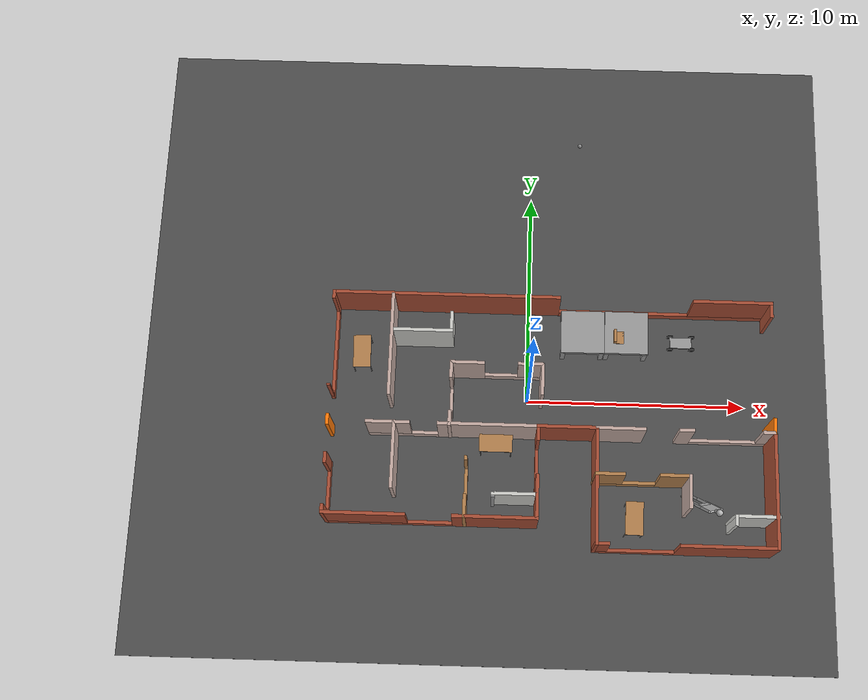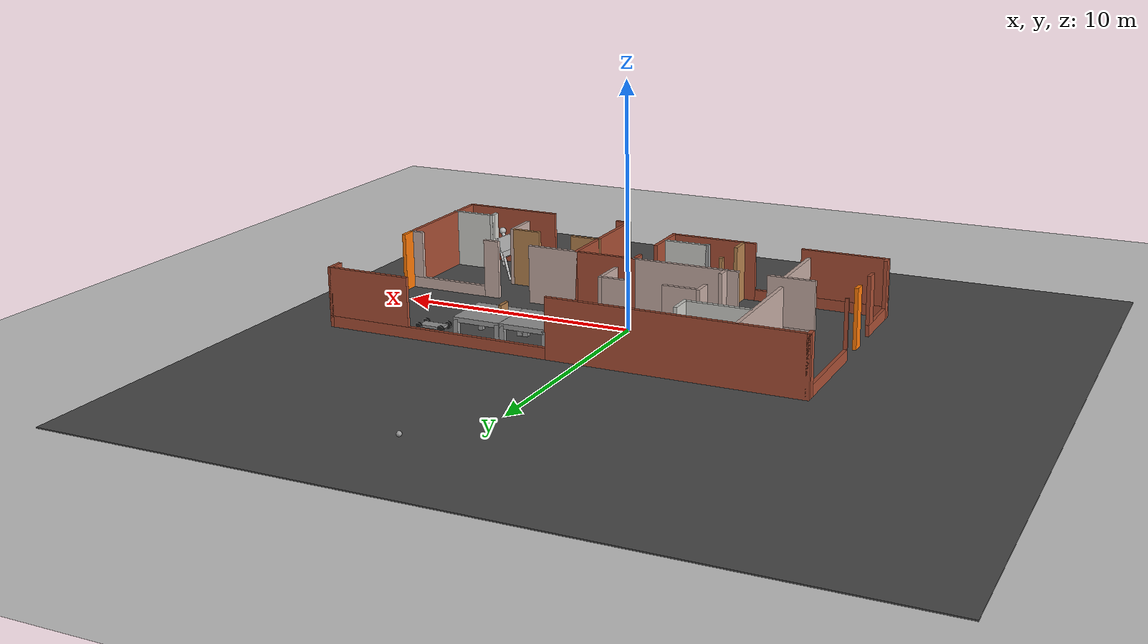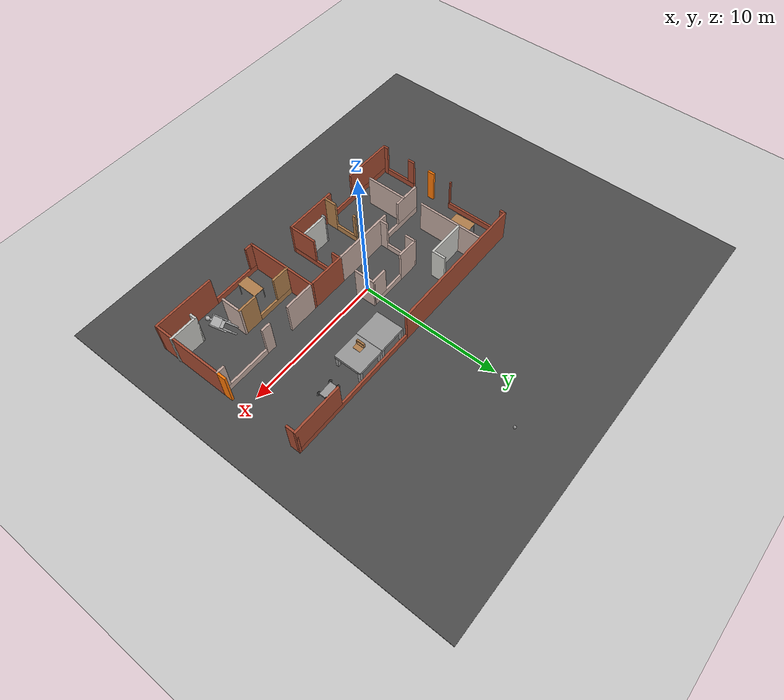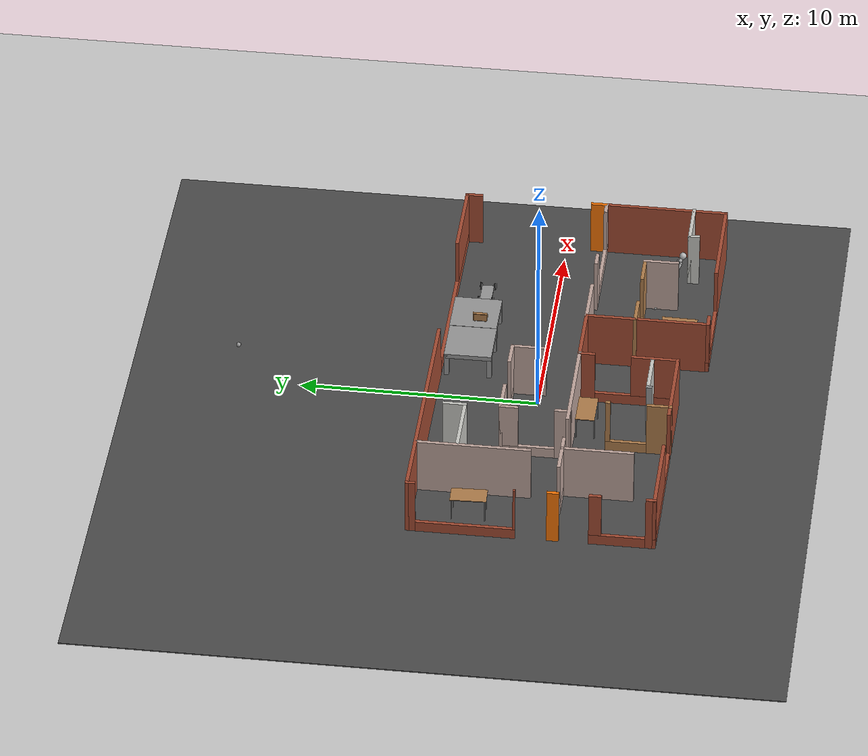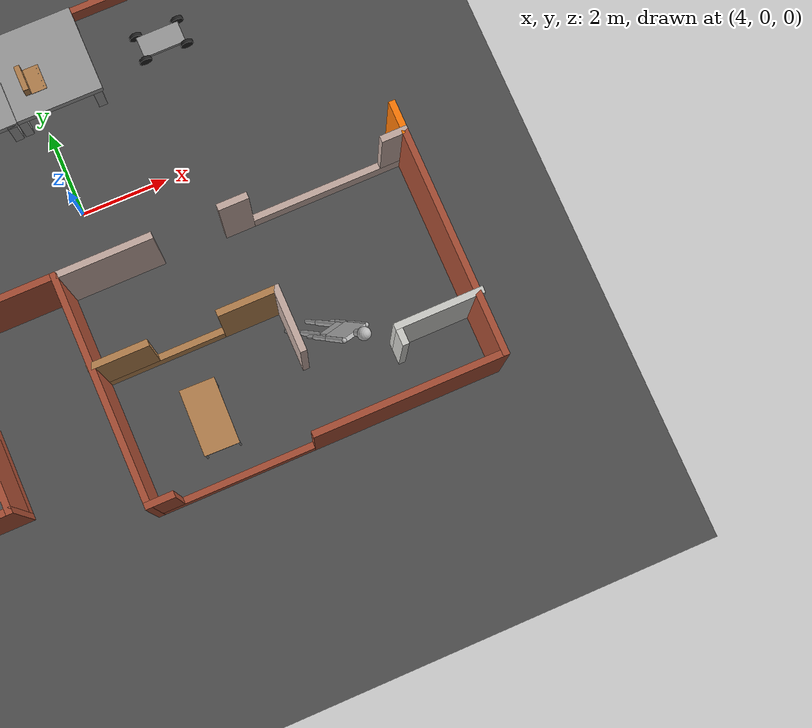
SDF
<sdf version="1.6">
 <world name="default">
  <light name="sun" type="directional">
   <pose>0 0 10 0 -0 0</pose>
   <diffuse>0.8 0.8 0.8 1</diffuse>
   <specular>0.2 0.2 0.2 1</specular>
   <attenuation>
    <range>1000</range>
    <constant>0.9</constant>
    <linear>0.01</linear>
    <quadratic>0.001</quadratic>
   </attenuation>
   <direction>-0.5 0.1 -0.9</direction>
  </light>
  <model name="ground_plane">
   <static>1</static>
   <link name="link">
    <collision name="collision">
     <geometry><plane><normal>0 0 1</normal><size>100 100</size></plane></geometry>
     <surface>
      <contact><collide_bitmask>65535</collide_bitmask></contact>
      <friction><ode><mu>100</mu><mu2>50</mu2></ode></friction>
     </surface>
    </collision>
    <visual name="visual">
     <cast_shadows>0</cast_shadows>
     <geometry><plane><normal>0 0 1</normal><size>100 100</size></plane></geometry>
     <material>
      <script><uri>file://media/materials/scripts/gazebo.material</uri><name>Gazebo/Grey</name></script>
     </material>
    </visual>
   </link>
  </model>
  <gravity>0 0 -9.8</gravity>
  <magnetic_field>6e-06 2.3e-05 -4.2e-05</magnetic_field>
  <atmosphere type="adiabatic"/>
  <physics name="default_physics" default="0" type="ode">
   <max_step_size>0.001</max_step_size>
   <real_time_factor>1</real_time_factor>
   <real_time_update_rate>1000</real_time_update_rate>
  </physics>
  <scene><ambient>0.4 0.4 0.4 1</ambient><background>0.7 0.7 0.7 1</background><shadows>1</shadows></scene>
  <spherical_coordinates>
   <surface_model>EARTH_WGS84</surface_model>
   <latitude_deg>0</latitude_deg>
   <longitude_deg>0</longitude_deg>
   <elevation>0</elevation>
   <heading_deg>0</heading_deg>
  </spherical_coordinates>
  <model name="bksFloor">
   <pose>1.04636 -1.22829 -0.033581 0 -0 0</pose>
   <link name="Wall_1">
    <pose>-0.029228 5.55 0 0 -0 0</pose>
    <visual name="Wall_1_Visual_0">
     <pose>-4.80896 0 1.25 0 -0 0</pose>
     <geometry><box><size>10.3821 0.15 2.5</size></box></geometry>
     <material>
      <script><uri>file://media/materials/scripts/gazebo.material</uri><name>Gazebo/Bricks</name></script>
      <ambient>1 1 1 1</ambient>
     </material>
     <meta><layer>0</layer></meta>
    </visual>
    <collision name="Wall_1_Collision_0">
     <geometry><box><size>10.3821 0.15 2.5</size></box></geometry>
     <pose>-4.80896 0 1.25 0 -0 0</pose>
    </collision>
    <visual name="Wall_1_Visual_1">
     <pose>5.19104 0 0.25 0 -0 0</pose>
     <geometry><box><size>9.61793 0.15 0.5</size></box></geometry>
     <material>
      <script><uri>file://media/materials/scripts/gazebo.material</uri><name>Gazebo/Bricks</name></script>
      <ambient>1 1 1 1</ambient>
     </material>
     <meta><layer>0</layer></meta>
    </visual>
    <collision name="Wall_1_Collision_1">
     <geometry><box><size>9.61793 0.15 0.5</size></box></geometry>
     <pose>5.19104 0 0.25 0 -0 0</pose>
    </collision>
    <visual name="Wall_1_Visual_2">
     <pose>8.19104 0 1.5 0 -0 0</pose>
     <geometry><box><size>3.61793 0.15 2</size></box></geometry>
     <material>
      <script><uri>file://media/materials/scripts/gazebo.material</uri><name>Gazebo/Bricks</name></script>
      <ambient>1 1 1 1</ambient>
     </material>
     <meta><layer>0</layer></meta>
    </visual>
    <collision name="Wall_1_Collision_2">
     <geometry><box><size>3.61793 0.15 2</size></box></geometry>
     <pose>8.19104 0 1.5 0 -0 0</pose>
    </collision>
   </link>
   <link name="Wall_12">
    <pose>-5.22923 -4.55 0 0 -0 3.14159</pose>
    <visual name="Wall_12_Visual_0">
     <pose>-2.85664 0 1.25 0 -0 0</pose>
     <geometry><box><size>3.78673 0.15 2.5</size></box></geometry>
     <material>
      <script><uri>file://media/materials/scripts/gazebo.material</uri><name>Gazebo/Bricks</name></script>
      <ambient>1 1 1 1</ambient>
     </material>
     <meta><layer>0</layer></meta>
    </visual>
    <collision name="Wall_12_Collision_0">
     <geometry><box><size>3.78673 0.15 2.5</size></box></geometry>
     <pose>-2.85664 0 1.25 0 -0 0</pose>
    </collision>
    <visual name="Wall_12_Visual_1">
     <pose>1.89336 0 0.25 0 -0 0</pose>
     <geometry><box><size>5.71328 0.15 0.5</size></box></geometry>
     <material>
      <script><uri>file://media/materials/scripts/gazebo.material</uri><name>Gazebo/Bricks</name></script>
      <ambient>1 1 1 1</ambient>
     </material>
     <meta><layer>0</layer></meta>
    </visual>
    <collision name="Wall_12_Collision_1">
     <geometry><box><size>5.71328 0.15 0.5</size></box></geometry>
     <pose>1.89336 0 0.25 0 -0 0</pose>
    </collision>
    <visual name="Wall_12_Visual_2">
     <pose>2.89336 0 1.5 0 -0 0</pose>
     <geometry><box><size>3.71327 0.15 2</size></box></geometry>
     <material>
      <script><uri>file://media/materials/scripts/gazebo.material</uri><name>Gazebo/Bricks</name></script>
      <ambient>1 1 1 1</ambient>
     </material>
     <meta><layer>0</layer></meta>
    </visual>
    <collision name="Wall_12_Collision_2">
     <geometry><box><size>3.71327 0.15 2</size></box></geometry>
     <pose>2.89336 0 1.5 0 -0 0</pose>
    </collision>
   </link>
   <link name="Wall_21">
    <pose>4.08581 -2.49345 0 0 -0 3.14159</pose>
    <visual name="Wall_21_Visual_0">
     <pose>-1.4228 0 1.25 0 -0 0</pose>
     <geometry><box><size>1.40439 0.15 2.5</size></box></geometry>
     <material>
      <script><uri>file://media/materials/scripts/gazebo.material</uri><name>Gazebo/Wood</name></script>
      <ambient>1 1 1 1</ambient>
     </material>
     <meta><layer>0</layer></meta>
    </visual>
    <collision name="Wall_21_Collision_0">
     <geometry><box><size>1.40439 0.15 2.5</size></box></geometry>
     <pose>-1.4228 0 1.25 0 -0 0</pose>
    </collision>
    <visual name="Wall_21_Visual_1">
     <pose>0.702197 0 0.25 0 -0 0</pose>
     <geometry><box><size>2.84561 0.15 0.5</size></box></geometry>
     <material>
      <script><uri>file://media/materials/scripts/gazebo.material</uri><name>Gazebo/Wood</name></script>
      <ambient>1 1 1 1</ambient>
     </material>
     <meta><layer>0</layer></meta>
    </visual>
    <collision name="Wall_21_Collision_1">
     <geometry><box><size>2.84561 0.15 0.5</size></box></geometry>
     <pose>0.702197 0 0.25 0 -0 0</pose>
    </collision>
    <visual name="Wall_21_Visual_2">
     <pose>1.4522 0 1.5 0 -0 0</pose>
     <geometry><box><size>1.34561 0.15 2</size></box></geometry>
     <material>
      <script><uri>file://media/materials/scripts/gazebo.material</uri><name>Gazebo/Wood</name></script>
      <ambient>1 1 1 1</ambient>
     </material>
     <meta><layer>0</layer></meta>
    </visual>
    <collision name="Wall_21_Collision_2">
     <geometry><box><size>1.34561 0.15 2</size></box></geometry>
     <pose>1.4522 0 1.5 0 -0 0</pose>
    </collision>
   </link>
   <link name="Wall_24">
    <collision name="Wall_24_Collision">
     <geometry><box><size>2 0.15 2.5</size></box></geometry>
     <pose>0 0 1.25 0 -0 0</pose>
    </collision>
    <visual name="Wall_24_Visual">
     <pose>0 0 1.25 0 -0 0</pose>
     <geometry><box><size>2 0.15 2.5</size></box></geometry>
     <material>
      <script><uri>file://media/materials/scripts/gazebo.material</uri><name>Gazebo/CeilingTiled</name></script>
      <ambient>1 1 1 1</ambient>
     </material>
     <meta><layer>0</layer></meta>
    </visual>
    <pose>9.02923 -4.19025 0 0 -0 0</pose>
   </link>
   <link name="Wall_3">
    <pose>5.97077 -5.55 0 0 -0 3.14159</pose>
    <visual name="Wall_3_Visual_0">
     <pose>-1.828 0 1.25 0 -0 0</pose>
     <geometry><box><size>4.34399 0.15 2.5</size></box></geometry>
     <material>
      <script><uri>file://media/materials/scripts/gazebo.material</uri><name>Gazebo/Bricks</name></script>
      <ambient>1 1 1 1</ambient>
     </material>
     <meta><layer>0</layer></meta>
    </visual>
    <collision name="Wall_3_Collision_0">
     <geometry><box><size>4.34399 0.15 2.5</size></box></geometry>
     <pose>-1.828 0 1.25 0 -0 0</pose>
    </collision>
    <visual name="Wall_3_Visual_1">
     <pose>2.172 0 0.25 0 -0 0</pose>
     <geometry><box><size>3.656 0.15 0.5</size></box></geometry>
     <material>
      <script><uri>file://media/materials/scripts/gazebo.material</uri><name>Gazebo/Bricks</name></script>
      <ambient>1 1 1 1</ambient>
     </material>
     <meta><layer>0</layer></meta>
    </visual>
    <collision name="Wall_3_Collision_1">
     <geometry><box><size>3.656 0.15 0.5</size></box></geometry>
     <pose>2.172 0 0.25 0 -0 0</pose>
    </collision>
    <visual name="Wall_3_Visual_2">
     <pose>3.672 0 1.5 0 -0 0</pose>
     <geometry><box><size>0.656005 0.15 2</size></box></geometry>
     <material>
      <script><uri>file://media/materials/scripts/gazebo.material</uri><name>Gazebo/Bricks</name></script>
      <ambient>1 1 1 1</ambient>
     </material>
     <meta><layer>0</layer></meta>
    </visual>
    <collision name="Wall_3_Collision_2">
     <geometry><box><size>0.656005 0.15 2</size></box></geometry>
     <pose>3.672 0 1.5 0 -0 0</pose>
    </collision>
   </link>
   <link name="Wall_34">
    <collision name="Wall_34_Collision">
     <geometry><box><size>0.75 0.15 2.5</size></box></geometry>
     <pose>0 0 1.25 0 -0 0</pose>
    </collision>
    <visual name="Wall_34_Visual">
     <pose>0 0 1.25 0 -0 0</pose>
     <geometry><box><size>0.75 0.15 2.5</size></box></geometry>
     <material>
      <script><uri>file://media/materials/scripts/gazebo.material</uri><name>Gazebo/Bricks</name></script>
      <ambient>1 1 1 1</ambient>
     </material>
     <meta><layer>0</layer></meta>
    </visual>
    <pose>9.89577 5.25 0 0 0 -1.5708</pose>
   </link>
   <link name="Wall_36">
    <collision name="Wall_36_Collision">
     <geometry><box><size>0.75 0.15 2.5</size></box></geometry>
     <pose>0 0 1.25 0 -0 0</pose>
    </collision>
    <visual name="Wall_36_Visual">
     <pose>0 0 1.25 0 -0 0</pose>
     <geometry><box><size>0.75 0.15 2.5</size></box></geometry>
     <material>
      <script><uri>file://media/materials/scripts/gazebo.material</uri><name>Gazebo/Grey</name></script>
      <ambient>0.996078 0.47451 0.0196078 1</ambient>
     </material>
     <meta><layer>0</layer></meta>
    </visual>
    <pose>9.89577 -0.15 0 0 -0 1.5708</pose>
   </link>
   <link name="Wall_38">
    <collision name="Wall_38_Collision">
     <geometry><box><size>5.25 0.15 2.5</size></box></geometry>
     <pose>0 0 1.25 0 -0 0</pose>
    </collision>
    <visual name="Wall_38_Visual">
     <pose>0 0 1.25 0 -0 0</pose>
     <geometry><box><size>5.25 0.15 2.5</size></box></geometry>
     <material>
      <script><uri>file://media/materials/scripts/gazebo.material</uri><name>Gazebo/Bricks</name></script>
      <ambient>1 1 1 1</ambient>
     </material>
     <meta><layer>0</layer></meta>
    </visual>
    <pose>9.89577 -3 0 0 0 -1.5708</pose>
   </link>
   <link name="Wall_4">
    <collision name="Wall_4_Collision">
     <geometry><box><size>5.25 0.15 2.5</size></box></geometry>
     <pose>0 0 1.25 0 -0 0</pose>
    </collision>
    <visual name="Wall_4_Visual">
     <pose>0 0 1.25 0 -0 0</pose>
     <geometry><box><size>5.25 0.15 2.5</size></box></geometry>
     <material>
      <script><uri>file://media/materials/scripts/gazebo.material</uri><name>Gazebo/Bricks</name></script>
      <ambient>1 1 1 1</ambient>
     </material>
     <meta><layer>0</layer></meta>
    </visual>
    <pose>2.04577 -3 0 0 -0 1.5708</pose>
   </link>
   <link name="Wall_40">
    <collision name="Wall_40_Collision">
     <geometry><box><size>0.5 0.15 2.5</size></box></geometry>
     <pose>0 0 1.25 0 -0 0</pose>
    </collision>
    <visual name="Wall_40_Visual">
     <pose>0 0 1.25 0 -0 0</pose>
     <geometry><box><size>0.5 0.15 2.5</size></box></geometry>
     <material>
      <script><uri>file://media/materials/scripts/gazebo.material</uri><name>Gazebo/CeilingTiled</name></script>
      <ambient>1 1 1 1</ambient>
     </material>
     <meta><layer>0</layer></meta>
    </visual>
    <pose>8.10423 -4.36525 0 0 0 -1.5708</pose>
   </link>
   <link name="Wall_42">
    <collision name="Wall_42_Collision">
     <geometry><box><size>1.5 0.15 2.5</size></box></geometry>
     <pose>0 0 1.25 0 -0 0</pose>
    </collision>
    <visual name="Wall_42_Visual">
     <pose>0 0 1.25 0 -0 0</pose>
     <geometry><box><size>1.5 0.15 2.5</size></box></geometry>
     <material>
      <script><uri>file://media/materials/scripts/gazebo.material</uri><name>Gazebo/Grey</name></script>
      <ambient>0.760784 0.662745 0.627451 1</ambient>
     </material>
     <meta><layer>0</layer></meta>
    </visual>
    <pose>6.13581 -3.16845 0 0 0 -1.5708</pose>
   </link>
   <link name="Wall_44">
    <pose>-9.95423 3.375 0 0 0 -1.5708</pose>
    <visual name="Wall_44_Visual_0">
     <pose>-2.04593 0 1.25 0 -0 0</pose>
     <geometry><box><size>0.408134 0.15 2.5</size></box></geometry>
     <material>
      <script><uri>file://media/materials/scripts/gazebo.material</uri><name>Gazebo/Bricks</name></script>
      <ambient>1 1 1 1</ambient>
     </material>
     <meta><layer>0</layer></meta>
    </visual>
    <collision name="Wall_44_Collision_0">
     <geometry><box><size>0.408134 0.15 2.5</size></box></geometry>
     <pose>-2.04593 0 1.25 0 -0 0</pose>
    </collision>
    <visual name="Wall_44_Visual_1">
     <pose>0.204067 0 0.25 0 -0 0</pose>
     <geometry><box><size>4.09187 0.15 0.5</size></box></geometry>
     <material>
      <script><uri>file://media/materials/scripts/gazebo.material</uri><name>Gazebo/Bricks</name></script>
      <ambient>1 1 1 1</ambient>
     </material>
     <meta><layer>0</layer></meta>
    </visual>
    <collision name="Wall_44_Collision_1">
     <geometry><box><size>4.09187 0.15 0.5</size></box></geometry>
     <pose>0.204067 0 0.25 0 -0 0</pose>
    </collision>
    <visual name="Wall_44_Visual_2">
     <pose>2.20407 0 1.5 0 -0 0</pose>
     <geometry><box><size>0.091866 0.15 2</size></box></geometry>
     <material>
      <script><uri>file://media/materials/scripts/gazebo.material</uri><name>Gazebo/Bricks</name></script>
      <ambient>1 1 1 1</ambient>
     </material>
     <meta><layer>0</layer></meta>
    </visual>
    <collision name="Wall_44_Collision_2">
     <geometry><box><size>0.091866 0.15 2</size></box></geometry>
     <pose>2.20407 0 1.5 0 -0 0</pose>
    </collision>
   </link>
   <link name="Wall_46">
    <pose>-9.90423 -3.25 0 0 -0 1.5708</pose>
    <visual name="Wall_46_Visual_0">
     <pose>-1.1581 0 1.25 0 -0 0</pose>
     <geometry><box><size>0.433795 0.15 2.5</size></box></geometry>
     <material>
      <script><uri>file://media/materials/scripts/gazebo.material</uri><name>Gazebo/Bricks</name></script>
      <ambient>1 1 1 1</ambient>
     </material>
     <meta><layer>0</layer></meta>
    </visual>
    <collision name="Wall_46_Collision_0">
     <geometry><box><size>0.433795 0.15 2.5</size></box></geometry>
     <pose>-1.1581 0 1.25 0 -0 0</pose>
    </collision>
    <visual name="Wall_46_Visual_1">
     <pose>0.216898 0 0.25 0 -0 0</pose>
     <geometry><box><size>2.31621 0.15 0.5</size></box></geometry>
     <material>
      <script><uri>file://media/materials/scripts/gazebo.material</uri><name>Gazebo/Bricks</name></script>
      <ambient>1 1 1 1</ambient>
     </material>
     <meta><layer>0</layer></meta>
    </visual>
    <collision name="Wall_46_Collision_1">
     <geometry><box><size>2.31621 0.15 0.5</size></box></geometry>
     <pose>0.216898 0 0.25 0 -0 0</pose>
    </collision>
    <visual name="Wall_46_Visual_2">
     <pose>1.1169 0 1.5 0 -0 0</pose>
     <geometry><box><size>0.516205 0.15 2</size></box></geometry>
     <material>
      <script><uri>file://media/materials/scripts/gazebo.material</uri><name>Gazebo/Bricks</name></script>
      <ambient>1 1 1 1</ambient>
     </material>
     <meta><layer>0</layer></meta>
    </visual>
    <collision name="Wall_46_Collision_2">
     <geometry><box><size>0.516205 0.15 2</size></box></geometry>
     <pose>1.1169 0 1.5 0 -0 0</pose>
    </collision>
   </link>
   <link name="Wall_48">
    <collision name="Wall_48_Collision">
     <geometry><box><size>3 0.15 2.5</size></box></geometry>
     <pose>0 0 1.25 0 -0 0</pose>
    </collision>
    <visual name="Wall_48_Visual">
     <pose>0 0 1.25 0 -0 0</pose>
     <geometry><box><size>3 0.15 2.5</size></box></geometry>
     <material>
      <script><uri>file://media/materials/scripts/gazebo.material</uri><name>Gazebo/Grey</name></script>
      <ambient>0.760784 0.662745 0.627451 1</ambient>
     </material>
     <meta><layer>0</layer></meta>
    </visual>
    <pose>-6.95794 -1.90503 0 0 0 -1.5708</pose>
   </link>
   <link name="Wall_5">
    <collision name="Wall_5_Collision">
     <geometry><box><size>2.75 0.15 2.5</size></box></geometry>
     <pose>0 0 1.25 0 -0 0</pose>
    </collision>
    <visual name="Wall_5_Visual">
     <pose>0 0 1.25 0 -0 0</pose>
     <geometry><box><size>2.75 0.15 2.5</size></box></geometry>
     <material>
      <script><uri>file://media/materials/scripts/gazebo.material</uri><name>Gazebo/Bricks</name></script>
      <ambient>1 1 1 1</ambient>
     </material>
     <meta><layer>0</layer></meta>
    </visual>
    <pose>0.745772 -0.45 0 0 -0 3.14159</pose>
   </link>
   <link name="Wall_50">
    <pose>-3.72149 -3.26076 0 0 -0 1.5708</pose>
    <visual name="Wall_50_Visual_0">
     <pose>-0.849058 0 1.25 0 -0 0</pose>
     <geometry><box><size>1.05188 0.15 2.5</size></box></geometry>
     <material>
      <script><uri>file://media/materials/scripts/gazebo.material</uri><name>Gazebo/Wood</name></script>
      <ambient>0.760784 0.662745 0.627451 1</ambient>
     </material>
     <meta><layer>0</layer></meta>
    </visual>
    <collision name="Wall_50_Collision_0">
     <geometry><box><size>1.05188 0.15 2.5</size></box></geometry>
     <pose>-0.849058 0 1.25 0 -0 0</pose>
    </collision>
    <visual name="Wall_50_Visual_1">
     <pose>0.525942 0 0.25 0 -0 0</pose>
     <geometry><box><size>1.69812 0.15 0.5</size></box></geometry>
     <material>
      <script><uri>file://media/materials/scripts/gazebo.material</uri><name>Gazebo/Wood</name></script>
      <ambient>0.760784 0.662745 0.627451 1</ambient>
     </material>
     <meta><layer>0</layer></meta>
    </visual>
    <collision name="Wall_50_Collision_1">
     <geometry><box><size>1.69812 0.15 0.5</size></box></geometry>
     <pose>0.525942 0 0.25 0 -0 0</pose>
    </collision>
    <visual name="Wall_50_Visual_2">
     <pose>1.27594 0 1.5 0 -0 0</pose>
     <geometry><box><size>0.198117 0.15 2</size></box></geometry>
     <material>
      <script><uri>file://media/materials/scripts/gazebo.material</uri><name>Gazebo/Wood</name></script>
      <ambient>0.760784 0.662745 0.627451 1</ambient>
     </material>
     <meta><layer>0</layer></meta>
    </visual>
    <collision name="Wall_50_Collision_2">
     <geometry><box><size>0.198117 0.15 2</size></box></geometry>
     <pose>1.27594 0 1.5 0 -0 0</pose>
    </collision>
   </link>
   <link name="Wall_54">
    <pose>-4.35423 -0.45 0 0 -0 3.14159</pose>
    <visual name="Wall_54_Visual_0">
     <pose>-1.58815 0 1.25 0 -0 0</pose>
     <geometry><box><size>4.57369 0.15 2.5</size></box></geometry>
     <material>
      <script><uri>file://media/materials/scripts/gazebo.material</uri><name>Gazebo/Grey</name></script>
      <ambient>0.760784 0.662745 0.627451 1</ambient>
     </material>
     <meta><layer>0</layer></meta>
    </visual>
    <collision name="Wall_54_Collision_0">
     <geometry><box><size>4.57369 0.15 2.5</size></box></geometry>
     <pose>-1.58815 0 1.25 0 -0 0</pose>
    </collision>
    <visual name="Wall_54_Visual_1">
     <pose>2.28685 0 0.25 0 -0 0</pose>
     <geometry><box><size>3.17631 0.15 0.5</size></box></geometry>
     <material>
      <script><uri>file://media/materials/scripts/gazebo.material</uri><name>Gazebo/Grey</name></script>
      <ambient>0.760784 0.662745 0.627451 1</ambient>
     </material>
     <meta><layer>0</layer></meta>
    </visual>
    <collision name="Wall_54_Collision_1">
     <geometry><box><size>3.17631 0.15 0.5</size></box></geometry>
     <pose>2.28685 0 0.25 0 -0 0</pose>
    </collision>
    <visual name="Wall_54_Visual_2">
     <pose>2.88685 0 1.5 0 -0 0</pose>
     <geometry><box><size>1.97631 0.15 2</size></box></geometry>
     <material>
      <script><uri>file://media/materials/scripts/gazebo.material</uri><name>Gazebo/Grey</name></script>
      <ambient>0.760784 0.662745 0.627451 1</ambient>
     </material>
     <meta><layer>0</layer></meta>
    </visual>
    <collision name="Wall_54_Collision_2">
     <geometry><box><size>1.97631 0.15 2</size></box></geometry>
     <pose>2.88685 0 1.5 0 -0 0</pose>
    </collision>
   </link>
   <link name="Wall_56">
    <collision name="Wall_56_Collision">
     <geometry><box><size>0.5 0.15 2.5</size></box></geometry>
     <pose>0 0 1.25 0 -0 0</pose>
    </collision>
    <visual name="Wall_56_Visual">
     <pose>0 0 1.25 0 -0 0</pose>
     <geometry><box><size>0.5 0.15 2.5</size></box></geometry>
     <material>
      <script><uri>file://media/materials/scripts/gazebo.material</uri><name>Gazebo/Grey</name></script>
      <ambient>0.996078 0.47451 0.0196078 1</ambient>
     </material>
     <meta><layer>0</layer></meta>
    </visual>
    <pose>-9.91295 -0.410564 0 0 -0 1.5708</pose>
   </link>
   <link name="Wall_58">
    <collision name="Wall_58_Collision">
     <geometry><box><size>2 0.15 2.5</size></box></geometry>
     <pose>0 0 1.25 0 -0 0</pose>
    </collision>
    <visual name="Wall_58_Visual">
     <pose>0 0 1.25 0 -0 0</pose>
     <geometry><box><size>2 0.15 2.5</size></box></geometry>
     <material>
      <script><uri>file://media/materials/scripts/gazebo.material</uri><name>Gazebo/CeilingTiled</name></script>
      <ambient>0.760784 0.662745 0.627451 1</ambient>
     </material>
     <meta><layer>0</layer></meta>
    </visual>
    <pose>-1.56523 -3.5054 0 0 -0 0</pose>
   </link>
   <link name="Wall_6">
    <pose>-0.554228 -2.5 0 0 0 -1.5708</pose>
    <visual name="Wall_6_Visual_0">
     <pose>-1.76306 0 1.25 0 -0 0</pose>
     <geometry><box><size>0.723876 0.15 2.5</size></box></geometry>
     <material>
      <script><uri>file://media/materials/scripts/gazebo.material</uri><name>Gazebo/Bricks</name></script>
      <ambient>1 1 1 1</ambient>
     </material>
     <meta><layer>0</layer></meta>
    </visual>
    <collision name="Wall_6_Collision_0">
     <geometry><box><size>0.723876 0.15 2.5</size></box></geometry>
     <pose>-1.76306 0 1.25 0 -0 0</pose>
    </collision>
    <visual name="Wall_6_Visual_1">
     <pose>0.361938 0 0.25 0 -0 0</pose>
     <geometry><box><size>3.52612 0.15 0.5</size></box></geometry>
     <material>
      <script><uri>file://media/materials/scripts/gazebo.material</uri><name>Gazebo/Bricks</name></script>
      <ambient>1 1 1 1</ambient>
     </material>
     <meta><layer>0</layer></meta>
    </visual>
    <collision name="Wall_6_Collision_1">
     <geometry><box><size>3.52612 0.15 0.5</size></box></geometry>
     <pose>0.361938 0 0.25 0 -0 0</pose>
    </collision>
    <visual name="Wall_6_Visual_2">
     <pose>1.11194 0 1.5 0 -0 0</pose>
     <geometry><box><size>2.02612 0.15 2</size></box></geometry>
     <material>
      <script><uri>file://media/materials/scripts/gazebo.material</uri><name>Gazebo/Bricks</name></script>
      <ambient>1 1 1 1</ambient>
     </material>
     <meta><layer>0</layer></meta>
    </visual>
    <collision name="Wall_6_Collision_2">
     <geometry><box><size>2.02612 0.15 2</size></box></geometry>
     <pose>1.11194 0 1.5 0 -0 0</pose>
    </collision>
   </link>
   <link name="Wall_60">
    <collision name="Wall_60_Collision">
     <geometry><box><size>0.25 0.15 2.5</size></box></geometry>
     <pose>0 0 1.25 0 -0 0</pose>
    </collision>
    <visual name="Wall_60_Visual">
     <pose>0 0 1.25 0 -0 0</pose>
     <geometry><box><size>0.25 0.15 2.5</size></box></geometry>
     <material>
      <script><uri>file://media/materials/scripts/gazebo.material</uri><name>Gazebo/Grey</name></script>
      <ambient>1 1 1 1</ambient>
     </material>
     <meta><layer>0</layer></meta>
    </visual>
    <pose>-2.49024 -3.5554 0 0 0 -1.5708</pose>
   </link>
   <link name="Wall_62">
    <collision name="Wall_62_Collision">
     <geometry><box><size>4.75 0.15 2.5</size></box></geometry>
     <pose>0 0 1.25 0 -0 0</pose>
    </collision>
    <visual name="Wall_62_Visual">
     <pose>0 0 1.25 0 -0 0</pose>
     <geometry><box><size>4.75 0.15 2.5</size></box></geometry>
     <material>
      <script><uri>file://media/materials/scripts/gazebo.material</uri><name>Gazebo/Grey</name></script>
      <ambient>0.760784 0.662745 0.627451 1</ambient>
     </material>
     <meta><layer>0</layer></meta>
    </visual>
    <pose>-7.26332 3.16139 0 0 0 -1.5708</pose>
   </link>
   <link name="Wall_64">
    <collision name="Wall_64_Collision">
     <geometry><box><size>2.25 0.15 2.5</size></box></geometry>
     <pose>0 0 1.25 0 -0 0</pose>
    </collision>
    <visual name="Wall_64_Visual">
     <pose>0 0 1.25 0 -0 0</pose>
     <geometry><box><size>2.25 0.15 2.5</size></box></geometry>
     <material>
      <script><uri>file://media/materials/scripts/gazebo.material</uri><name>Gazebo/Grey</name></script>
      <ambient>0.760784 0.662745 0.627451 1</ambient>
     </material>
     <meta><layer>0</layer></meta>
    </visual>
    <pose>3.09577 -0.45 0 0 -0 0</pose>
   </link>
   <link name="Wall_66">
    <pose>7.82077 -0.45 0 0 -0 0</pose>
    <visual name="Wall_66_Visual_0">
     <pose>-1.80752 0 1.25 0 -0 0</pose>
     <geometry><box><size>0.684954 0.15 2.5</size></box></geometry>
     <material>
      <script><uri>file://media/materials/scripts/gazebo.material</uri><name>Gazebo/Grey</name></script>
      <ambient>0.760784 0.662745 0.627451 1</ambient>
     </material>
     <meta><layer>0</layer></meta>
    </visual>
    <collision name="Wall_66_Collision_0">
     <geometry><box><size>0.684954 0.15 2.5</size></box></geometry>
     <pose>-1.80752 0 1.25 0 -0 0</pose>
    </collision>
    <visual name="Wall_66_Visual_1">
     <pose>0.342477 0 0.25 0 -0 0</pose>
     <geometry><box><size>3.61505 0.15 0.5</size></box></geometry>
     <material>
      <script><uri>file://media/materials/scripts/gazebo.material</uri><name>Gazebo/Grey</name></script>
      <ambient>0.760784 0.662745 0.627451 1</ambient>
     </material>
     <meta><layer>0</layer></meta>
    </visual>
    <collision name="Wall_66_Collision_1">
     <geometry><box><size>3.61505 0.15 0.5</size></box></geometry>
     <pose>0.342477 0 0.25 0 -0 0</pose>
    </collision>
    <visual name="Wall_66_Visual_2">
     <pose>1.84248 0 1.5 0 -0 0</pose>
     <geometry><box><size>0.615046 0.15 2</size></box></geometry>
     <material>
      <script><uri>file://media/materials/scripts/gazebo.material</uri><name>Gazebo/Grey</name></script>
      <ambient>0.760784 0.662745 0.627451 1</ambient>
     </material>
     <meta><layer>0</layer></meta>
    </visual>
    <collision name="Wall_66_Collision_2">
     <geometry><box><size>0.615046 0.15 2</size></box></geometry>
     <pose>1.84248 0 1.5 0 -0 0</pose>
    </collision>
   </link>
   <link name="Wall_68">
    <collision name="Wall_68_Collision">
     <geometry><box><size>2.75 0.15 2.5</size></box></geometry>
     <pose>0 0 1.25 0 -0 0</pose>
    </collision>
    <visual name="Wall_68_Visual">
     <pose>0 0 1.25 0 -0 0</pose>
     <geometry><box><size>2.75 0.15 2.5</size></box></geometry>
     <material>
      <script><uri>file://media/materials/scripts/gazebo.material</uri><name>Gazebo/CeilingTiled</name></script>
      <ambient>0.760784 0.662745 0.627451 1</ambient>
     </material>
     <meta><layer>0</layer></meta>
    </visual>
    <pose>-5.87155 3.8401 0 0 -0 0</pose>
   </link>
   <link name="Wall_69">
    <collision name="Wall_69_Collision">
     <geometry><box><size>1 0.15 2.5</size></box></geometry>
     <pose>0 0 1.25 0 -0 0</pose>
    </collision>
    <visual name="Wall_69_Visual">
     <pose>0 0 1.25 0 -0 0</pose>
     <geometry><box><size>1 0.15 2.5</size></box></geometry>
     <material>
      <script><uri>file://media/materials/scripts/gazebo.material</uri><name>Gazebo/CeilingTiled</name></script>
      <ambient>0.760784 0.662745 0.627451 1</ambient>
     </material>
     <meta><layer>0</layer></meta>
    </visual>
    <pose>-4.57155 4.26511 0 0 -0 1.5708</pose>
   </link>
   <link name="Wall_75">
    <pose>-4.5102 0.951883 0 0 -0 1.5708</pose>
    <visual name="Wall_75_Visual_0">
     <pose>-1.15341 0 1.25 0 -0 0</pose>
     <geometry><box><size>0.693186 0.15 2.5</size></box></geometry>
     <material>
      <script><uri>file://media/materials/scripts/gazebo.material</uri><name>Gazebo/Grey</name></script>
      <ambient>0.760784 0.662745 0.627451 1</ambient>
     </material>
     <meta><layer>0</layer></meta>
    </visual>
    <collision name="Wall_75_Collision_0">
     <geometry><box><size>0.693186 0.15 2.5</size></box></geometry>
     <pose>-1.15341 0 1.25 0 -0 0</pose>
    </collision>
    <visual name="Wall_75_Visual_1">
     <pose>0.346593 0 0.25 0 -0 0</pose>
     <geometry><box><size>2.30681 0.15 0.5</size></box></geometry>
     <material>
      <script><uri>file://media/materials/scripts/gazebo.material</uri><name>Gazebo/Grey</name></script>
      <ambient>0.760784 0.662745 0.627451 1</ambient>
     </material>
     <meta><layer>0</layer></meta>
    </visual>
    <collision name="Wall_75_Collision_1">
     <geometry><box><size>2.30681 0.15 0.5</size></box></geometry>
     <pose>0.346593 0 0.25 0 -0 0</pose>
    </collision>
    <visual name="Wall_75_Visual_2">
     <pose>1.09659 0 1.5 0 -0 0</pose>
     <geometry><box><size>0.806814 0.15 2</size></box></geometry>
     <material>
      <script><uri>file://media/materials/scripts/gazebo.material</uri><name>Gazebo/Grey</name></script>
      <ambient>0.760784 0.662745 0.627451 1</ambient>
     </material>
     <meta><layer>0</layer></meta>
    </visual>
    <collision name="Wall_75_Collision_2">
     <geometry><box><size>0.806814 0.15 2</size></box></geometry>
     <pose>1.09659 0 1.5 0 -0 0</pose>
    </collision>
   </link>
   <link name="Wall_77">
    <pose>-2.4602 2.37688 0 0 -0 0</pose>
    <visual name="Wall_77_Visual_0">
     <pose>-1.34528 0 1.25 0 -0 0</pose>
     <geometry><box><size>1.55944 0.15 2.5</size></box></geometry>
     <material>
      <script><uri>file://media/materials/scripts/gazebo.material</uri><name>Gazebo/Grey</name></script>
      <ambient>0.760784 0.662745 0.627451 1</ambient>
     </material>
     <meta><layer>0</layer></meta>
    </visual>
    <collision name="Wall_77_Collision_0">
     <geometry><box><size>1.55944 0.15 2.5</size></box></geometry>
     <pose>-1.34528 0 1.25 0 -0 0</pose>
    </collision>
    <visual name="Wall_77_Visual_1">
     <pose>0.77972 0 0.25 0 -0 0</pose>
     <geometry><box><size>2.69056 0.15 0.5</size></box></geometry>
     <material>
      <script><uri>file://media/materials/scripts/gazebo.material</uri><name>Gazebo/Grey</name></script>
      <ambient>0.760784 0.662745 0.627451 1</ambient>
     </material>
     <meta><layer>0</layer></meta>
    </visual>
    <collision name="Wall_77_Collision_1">
     <geometry><box><size>2.69056 0.15 0.5</size></box></geometry>
     <pose>0.77972 0 0.25 0 -0 0</pose>
    </collision>
    <visual name="Wall_77_Visual_2">
     <pose>1.52972 0 1.5 0 -0 0</pose>
     <geometry><box><size>1.19056 0.15 2</size></box></geometry>
     <material>
      <script><uri>file://media/materials/scripts/gazebo.material</uri><name>Gazebo/Grey</name></script>
      <ambient>0.760784 0.662745 0.627451 1</ambient>
     </material>
     <meta><layer>0</layer></meta>
    </visual>
    <collision name="Wall_77_Collision_2">
     <geometry><box><size>1.19056 0.15 2</size></box></geometry>
     <pose>1.52972 0 1.5 0 -0 0</pose>
    </collision>
   </link>
   <link name="Wall_78">
    <collision name="Wall_78_Collision">
     <geometry><box><size>1.5 0.15 2.5</size></box></geometry>
     <pose>0 0 1.25 0 -0 0</pose>
    </collision>
    <visual name="Wall_78_Visual">
     <pose>0 0 1.25 0 -0 0</pose>
     <geometry><box><size>1.5 0.15 2.5</size></box></geometry>
     <material>
      <script><uri>file://media/materials/scripts/gazebo.material</uri><name>Gazebo/Grey</name></script>
      <ambient>0.760784 0.662745 0.627451 1</ambient>
     </material>
     <meta><layer>0</layer></meta>
    </visual>
    <pose>-0.410197 1.70188 0 0 0 -1.5708</pose>
   </link>
   <static>1</static>
  </model>
  <model name="TableSmall_clone">
   <link name="link_0">
    <pose>0.868 -0.9 -0.096 0 -0 0</pose>
    <inertial>
     <mass>1</mass>
     <inertia>
      <ixx>0.166667</ixx>
      <ixy>0</ixy>
      <ixz>0</ixz>
      <iyy>0.166667</iyy>
      <iyz>0</iyz>
      <izz>0.166667</izz>
     </inertia>
    </inertial>
    <visual name="visual">
     <geometry><box><size>0.2 0.2 1</size></box></geometry>
     <material>
      <lighting>1</lighting>
      <script><uri>file://media/materials/scripts/gazebo.material</uri><name>Gazebo/Grey</name></script>
      <shader type="pixel"><normal_map>__default__</normal_map></shader>
      <ambient>0.3 0.3 0.3 1</ambient>
      <diffuse>0.7 0.7 0.7 1</diffuse>
      <specular>0.01 0.01 0.01 1</specular>
      <emissive>0 0 0 1</emissive>
     </material>
    </visual>
    <collision name="collision">
     <geometry><box><size>0.2 0.2 1</size></box></geometry>
     <surface>
      <friction>
       <ode><mu>1</mu><mu2>1</mu2><fdir1>0 0 0</fdir1><slip1>0</slip1><slip2>0</slip2></ode>
       <torsional>
        <coefficient>1</coefficient>
        <patch_radius>0</patch_radius>
        <surface_radius>0</surface_radius>
        <use_patch_radius>1</use_patch_radius>
        <ode><slip>0</slip></ode>
       </torsional>
      </friction>
      <bounce><restitution_coefficient>0</restitution_coefficient><threshold>1e+06</threshold></bounce>
      <contact>
       <collide_without_contact>0</collide_without_contact>
       <collide_without_contact_bitmask>1</collide_without_contact_bitmask>
       <collide_bitmask>1</collide_bitmask>
       <ode>
        <soft_cfm>0</soft_cfm>
        <soft_erp>0.2</soft_erp>
        <kp>1e+13</kp>
        <kd>1</kd>
        <max_vel>0.01</max_vel>
        <min_depth>0</min_depth>
       </ode>
       <bullet>
        <split_impulse>1</split_impulse>
        <split_impulse_penetration_threshold>-0.01</split_impulse_penetration_threshold>
        <soft_cfm>0</soft_cfm>
        <soft_erp>0.2</soft_erp>
        <kp>1e+13</kp>
        <kd>1</kd>
       </bullet>
      </contact>
     </surface>
    </collision>
   </link>
   <link name="link_0_clone">
    <pose>-0.892 -0.9 -0.096 0 -0 0</pose>
    <inertial>
     <mass>1</mass>
     <inertia>
      <ixx>0.166667</ixx>
      <ixy>0</ixy>
      <ixz>0</ixz>
      <iyy>0.166667</iyy>
      <iyz>0</iyz>
      <izz>0.166667</izz>
     </inertia>
    </inertial>
    <visual name="visual">
     <geometry><box><size>0.2 0.2 1</size></box></geometry>
     <material>
      <lighting>1</lighting>
      <script><uri>file://media/materials/scripts/gazebo.material</uri><name>Gazebo/Grey</name></script>
      <shader type="pixel"><normal_map>__default__</normal_map></shader>
      <ambient>0.3 0.3 0.3 1</ambient>
      <diffuse>0.7 0.7 0.7 1</diffuse>
      <specular>0.01 0.01 0.01 1</specular>
      <emissive>0 0 0 1</emissive>
     </material>
    </visual>
    <collision name="collision">
     <geometry><box><size>0.2 0.2 1</size></box></geometry>
     <surface>
      <friction>
       <ode><mu>1</mu><mu2>1</mu2><fdir1>0 0 0</fdir1><slip1>0</slip1><slip2>0</slip2></ode>
       <torsional>
        <coefficient>1</coefficient>
        <patch_radius>0</patch_radius>
        <surface_radius>0</surface_radius>
        <use_patch_radius>1</use_patch_radius>
        <ode><slip>0</slip></ode>
       </torsional>
      </friction>
      <bounce><restitution_coefficient>0</restitution_coefficient><threshold>1e+06</threshold></bounce>
      <contact>
       <collide_without_contact>0</collide_without_contact>
       <collide_without_contact_bitmask>1</collide_without_contact_bitmask>
       <collide_bitmask>1</collide_bitmask>
       <ode>
        <soft_cfm>0</soft_cfm>
        <soft_erp>0.2</soft_erp>
        <kp>1e+13</kp>
        <kd>1</kd>
        <max_vel>0.01</max_vel>
        <min_depth>0</min_depth>
       </ode>
       <bullet>
        <split_impulse>1</split_impulse>
        <split_impulse_penetration_threshold>-0.01</split_impulse_penetration_threshold>
        <soft_cfm>0</soft_cfm>
        <soft_erp>0.2</soft_erp>
        <kp>1e+13</kp>
        <kd>1</kd>
       </bullet>
      </contact>
     </surface>
    </collision>
   </link>
   <link name="link_0_clone_0">
    <pose>-0.892 0.9 -0.096 0 -0 0</pose>
    <inertial>
     <mass>1</mass>
     <inertia>
      <ixx>0.166667</ixx>
      <ixy>0</ixy>
      <ixz>0</ixz>
      <iyy>0.166667</iyy>
      <iyz>0</iyz>
      <izz>0.166667</izz>
     </inertia>
    </inertial>
    <visual name="visual">
     <geometry><box><size>0.2 0.2 1</size></box></geometry>
     <material>
      <lighting>1</lighting>
      <script><uri>file://media/materials/scripts/gazebo.material</uri><name>Gazebo/Grey</name></script>
      <shader type="pixel"><normal_map>__default__</normal_map></shader>
      <ambient>0.3 0.3 0.3 1</ambient>
      <diffuse>0.7 0.7 0.7 1</diffuse>
      <specular>0.01 0.01 0.01 1</specular>
      <emissive>0 0 0 1</emissive>
     </material>
    </visual>
    <collision name="collision">
     <geometry><box><size>0.2 0.2 1</size></box></geometry>
     <surface>
      <friction>
       <ode><mu>1</mu><mu2>1</mu2><fdir1>0 0 0</fdir1><slip1>0</slip1><slip2>0</slip2></ode>
       <torsional>
        <coefficient>1</coefficient>
        <patch_radius>0</patch_radius>
        <surface_radius>0</surface_radius>
        <use_patch_radius>1</use_patch_radius>
        <ode><slip>0</slip></ode>
       </torsional>
      </friction>
      <bounce><restitution_coefficient>0</restitution_coefficient><threshold>1e+06</threshold></bounce>
      <contact>
       <collide_without_contact>0</collide_without_contact>
       <collide_without_contact_bitmask>1</collide_without_contact_bitmask>
       <collide_bitmask>1</collide_bitmask>
       <ode>
        <soft_cfm>0</soft_cfm>
        <soft_erp>0.2</soft_erp>
        <kp>1e+13</kp>
        <kd>1</kd>
        <max_vel>0.01</max_vel>
        <min_depth>0</min_depth>
       </ode>
       <bullet>
        <split_impulse>1</split_impulse>
        <split_impulse_penetration_threshold>-0.01</split_impulse_penetration_threshold>
        <soft_cfm>0</soft_cfm>
        <soft_erp>0.2</soft_erp>
        <kp>1e+13</kp>
        <kd>1</kd>
       </bullet>
      </contact>
     </surface>
    </collision>
   </link>
   <link name="link_0_clone_1">
    <pose>0.908 0.9 -0.096 0 -0 0</pose>
    <inertial>
     <mass>1</mass>
     <inertia>
      <ixx>0.166667</ixx>
      <ixy>0</ixy>
      <ixz>0</ixz>
      <iyy>0.166667</iyy>
      <iyz>0</iyz>
      <izz>0.166667</izz>
     </inertia>
    </inertial>
    <visual name="visual">
     <geometry><box><size>0.2 0.2 1</size></box></geometry>
     <material>
      <lighting>1</lighting>
      <script><uri>file://media/materials/scripts/gazebo.material</uri><name>Gazebo/Grey</name></script>
      <shader type="pixel"><normal_map>__default__</normal_map></shader>
      <ambient>0.3 0.3 0.3 1</ambient>
      <diffuse>0.7 0.7 0.7 1</diffuse>
      <specular>0.01 0.01 0.01 1</specular>
      <emissive>0 0 0 1</emissive>
     </material>
    </visual>
    <collision name="collision">
     <geometry><box><size>0.2 0.2 1</size></box></geometry>
     <surface>
      <friction>
       <ode><mu>1</mu><mu2>1</mu2><fdir1>0 0 0</fdir1><slip1>0</slip1><slip2>0</slip2></ode>
       <torsional>
        <coefficient>1</coefficient>
        <patch_radius>0</patch_radius>
        <surface_radius>0</surface_radius>
        <use_patch_radius>1</use_patch_radius>
        <ode><slip>0</slip></ode>
       </torsional>
      </friction>
      <bounce><restitution_coefficient>0</restitution_coefficient><threshold>1e+06</threshold></bounce>
      <contact>
       <collide_without_contact>0</collide_without_contact>
       <collide_without_contact_bitmask>1</collide_without_contact_bitmask>
       <collide_bitmask>1</collide_bitmask>
       <ode>
        <soft_cfm>0</soft_cfm>
        <soft_erp>0.2</soft_erp>
        <kp>1e+13</kp>
        <kd>1</kd>
        <max_vel>0.01</max_vel>
        <min_depth>0</min_depth>
       </ode>
       <bullet>
        <split_impulse>1</split_impulse>
        <split_impulse_penetration_threshold>-0.01</split_impulse_penetration_threshold>
        <soft_cfm>0</soft_cfm>
        <soft_erp>0.2</soft_erp>
        <kp>1e+13</kp>
        <kd>1</kd>
       </bullet>
      </contact>
     </surface>
    </collision>
   </link>
   <link name="link_1">
    <pose>0.008 0 0.384 0 -0 0</pose>
    <inertial>
     <mass>1</mass>
     <inertia>
      <ixx>0.166667</ixx>
      <ixy>0</ixy>
      <ixz>0</ixz>
      <iyy>0.166667</iyy>
      <iyz>0</iyz>
      <izz>0.166667</izz>
     </inertia>
    </inertial>
    <visual name="visual">
     <geometry><box><size>2 2 0.2</size></box></geometry>
     <material>
      <lighting>1</lighting>
      <script><uri>file://media/materials/scripts/gazebo.material</uri><name>Gazebo/Grey</name></script>
      <shader type="pixel"><normal_map>__default__</normal_map></shader>
      <ambient>0.3 0.3 0.3 1</ambient>
      <diffuse>0.7 0.7 0.7 1</diffuse>
      <specular>0.01 0.01 0.01 1</specular>
      <emissive>0 0 0 1</emissive>
     </material>
    </visual>
    <collision name="collision">
     <geometry><box><size>2 2 0.2</size></box></geometry>
     <surface>
      <friction>
       <ode><mu>1</mu><mu2>1</mu2><fdir1>0 0 0</fdir1><slip1>0</slip1><slip2>0</slip2></ode>
       <torsional>
        <coefficient>1</coefficient>
        <patch_radius>0</patch_radius>
        <surface_radius>0</surface_radius>
        <use_patch_radius>1</use_patch_radius>
        <ode><slip>0</slip></ode>
       </torsional>
      </friction>
      <bounce><restitution_coefficient>0</restitution_coefficient><threshold>1e+06</threshold></bounce>
      <contact>
       <collide_without_contact>0</collide_without_contact>
       <collide_without_contact_bitmask>1</collide_without_contact_bitmask>
       <collide_bitmask>1</collide_bitmask>
       <ode>
        <soft_cfm>0</soft_cfm>
        <soft_erp>0.2</soft_erp>
        <kp>1e+13</kp>
        <kd>1</kd>
        <max_vel>0.01</max_vel>
        <min_depth>0</min_depth>
       </ode>
       <bullet>
        <split_impulse>1</split_impulse>
        <split_impulse_penetration_threshold>-0.01</split_impulse_penetration_threshold>
        <soft_cfm>0</soft_cfm>
        <soft_erp>0.2</soft_erp>
        <kp>1e+13</kp>
        <kd>1</kd>
       </bullet>
      </contact>
     </surface>
    </collision>
   </link>
   <joint name="link_1_JOINT_0" type="fixed">
    <parent>link_1</parent>
    <child>link_0_clone_1</child>
    <physics>
     <ode><limit><cfm>0</cfm><erp>0.2</erp></limit><suspension><cfm>0</cfm><erp>0.2</erp></suspension></ode>
    </physics>
   </joint>
   <joint name="link_1_JOINT_1" type="fixed">
    <parent>link_1</parent>
    <child>link_0_clone_0</child>
    <physics>
     <ode><limit><cfm>0</cfm><erp>0.2</erp></limit><suspension><cfm>0</cfm><erp>0.2</erp></suspension></ode>
    </physics>
   </joint>
   <joint name="link_1_JOINT_2" type="revolute">
    <parent>link_1</parent>
    <child>link_0</child>
    <axis>
     <xyz>1 0 0</xyz>
     <use_parent_model_frame>0</use_parent_model_frame>
     <limit>
      <lower>-1.79769e+308</lower>
      <upper>1.79769e+308</upper>
      <effort>-1</effort>
      <velocity>-1</velocity>
     </limit>
     <dynamics>
      <spring_reference>0</spring_reference>
      <spring_stiffness>0</spring_stiffness>
      <damping>0</damping>
     </dynamics>
    </axis>
    <physics>
     <ode><limit><cfm>0</cfm><erp>0.2</erp></limit><suspension><cfm>0</cfm><erp>0.2</erp></suspension></ode>
    </physics>
   </joint>
   <joint name="link_1_JOINT_3" type="revolute">
    <parent>link_1</parent>
    <child>link_0_clone</child>
    <axis>
     <xyz>1 0 0</xyz>
     <use_parent_model_frame>0</use_parent_model_frame>
     <limit>
      <lower>-1.79769e+308</lower>
      <upper>1.79769e+308</upper>
      <effort>-1</effort>
      <velocity>-1</velocity>
     </limit>
     <dynamics>
      <spring_reference>0</spring_reference>
      <spring_stiffness>0</spring_stiffness>
      <damping>0</damping>
     </dynamics>
    </axis>
    <physics>
     <ode><limit><cfm>0</cfm><erp>0.2</erp></limit><suspension><cfm>0</cfm><erp>0.2</erp></suspension></ode>
    </physics>
   </joint>
   <static>0</static>
   <pose>4.49155 3.16061 0.598001 4e-06 4e-06 -0.001695</pose>
  </model>
  <model name="TableSmall_clone_clone">
   <link name="link_0">
    <pose>0.868 -0.9 -0.096 0 -0 0</pose>
    <inertial>
     <mass>1</mass>
     <inertia>
      <ixx>0.166667</ixx>
      <ixy>0</ixy>
      <ixz>0</ixz>
      <iyy>0.166667</iyy>
      <iyz>0</iyz>
      <izz>0.166667</izz>
     </inertia>
    </inertial>
    <visual name="visual">
     <geometry><box><size>0.2 0.2 1</size></box></geometry>
     <material>
      <lighting>1</lighting>
      <script><uri>file://media/materials/scripts/gazebo.material</uri><name>Gazebo/Grey</name></script>
      <shader type="pixel"><normal_map>__default__</normal_map></shader>
      <ambient>0.3 0.3 0.3 1</ambient>
      <diffuse>0.7 0.7 0.7 1</diffuse>
      <specular>0.01 0.01 0.01 1</specular>
      <emissive>0 0 0 1</emissive>
     </material>
    </visual>
    <collision name="collision">
     <geometry><box><size>0.2 0.2 1</size></box></geometry>
     <surface>
      <friction>
       <ode><mu>1</mu><mu2>1</mu2><fdir1>0 0 0</fdir1><slip1>0</slip1><slip2>0</slip2></ode>
       <torsional>
        <coefficient>1</coefficient>
        <patch_radius>0</patch_radius>
        <surface_radius>0</surface_radius>
        <use_patch_radius>1</use_patch_radius>
        <ode><slip>0</slip></ode>
       </torsional>
      </friction>
      <bounce><restitution_coefficient>0</restitution_coefficient><threshold>1e+06</threshold></bounce>
      <contact>
       <collide_without_contact>0</collide_without_contact>
       <collide_without_contact_bitmask>1</collide_without_contact_bitmask>
       <collide_bitmask>1</collide_bitmask>
       <ode>
        <soft_cfm>0</soft_cfm>
        <soft_erp>0.2</soft_erp>
        <kp>1e+13</kp>
        <kd>1</kd>
        <max_vel>0.01</max_vel>
        <min_depth>0</min_depth>
       </ode>
       <bullet>
        <split_impulse>1</split_impulse>
        <split_impulse_penetration_threshold>-0.01</split_impulse_penetration_threshold>
        <soft_cfm>0</soft_cfm>
        <soft_erp>0.2</soft_erp>
        <kp>1e+13</kp>
        <kd>1</kd>
       </bullet>
      </contact>
     </surface>
    </collision>
   </link>
   <link name="link_0_clone">
    <pose>-0.892 -0.9 -0.096 0 -0 0</pose>
    <inertial>
     <mass>1</mass>
     <inertia>
      <ixx>0.166667</ixx>
      <ixy>0</ixy>
      <ixz>0</ixz>
      <iyy>0.166667</iyy>
      <iyz>0</iyz>
      <izz>0.166667</izz>
     </inertia>
    </inertial>
    <visual name="visual">
     <geometry><box><size>0.2 0.2 1</size></box></geometry>
     <material>
      <lighting>1</lighting>
      <script><uri>file://media/materials/scripts/gazebo.material</uri><name>Gazebo/Grey</name></script>
      <shader type="pixel"><normal_map>__default__</normal_map></shader>
      <ambient>0.3 0.3 0.3 1</ambient>
      <diffuse>0.7 0.7 0.7 1</diffuse>
      <specular>0.01 0.01 0.01 1</specular>
      <emissive>0 0 0 1</emissive>
     </material>
    </visual>
    <collision name="collision">
     <geometry><box><size>0.2 0.2 1</size></box></geometry>
     <surface>
      <friction>
       <ode><mu>1</mu><mu2>1</mu2><fdir1>0 0 0</fdir1><slip1>0</slip1><slip2>0</slip2></ode>
       <torsional>
        <coefficient>1</coefficient>
        <patch_radius>0</patch_radius>
        <surface_radius>0</surface_radius>
        <use_patch_radius>1</use_patch_radius>
        <ode><slip>0</slip></ode>
       </torsional>
      </friction>
      <bounce><restitution_coefficient>0</restitution_coefficient><threshold>1e+06</threshold></bounce>
      <contact>
       <collide_without_contact>0</collide_without_contact>
       <collide_without_contact_bitmask>1</collide_without_contact_bitmask>
       <collide_bitmask>1</collide_bitmask>
       <ode>
        <soft_cfm>0</soft_cfm>
        <soft_erp>0.2</soft_erp>
        <kp>1e+13</kp>
        <kd>1</kd>
        <max_vel>0.01</max_vel>
        <min_depth>0</min_depth>
       </ode>
       <bullet>
        <split_impulse>1</split_impulse>
        <split_impulse_penetration_threshold>-0.01</split_impulse_penetration_threshold>
        <soft_cfm>0</soft_cfm>
        <soft_erp>0.2</soft_erp>
        <kp>1e+13</kp>
        <kd>1</kd>
       </bullet>
      </contact>
     </surface>
    </collision>
   </link>
   <link name="link_0_clone_0">
    <pose>-0.892 0.9 -0.096 0 -0 0</pose>
    <inertial>
     <mass>1</mass>
     <inertia>
      <ixx>0.166667</ixx>
      <ixy>0</ixy>
      <ixz>0</ixz>
      <iyy>0.166667</iyy>
      <iyz>0</iyz>
      <izz>0.166667</izz>
     </inertia>
    </inertial>
    <visual name="visual">
     <geometry><box><size>0.2 0.2 1</size></box></geometry>
     <material>
      <lighting>1</lighting>
      <script><uri>file://media/materials/scripts/gazebo.material</uri><name>Gazebo/Grey</name></script>
      <shader type="pixel"><normal_map>__default__</normal_map></shader>
      <ambient>0.3 0.3 0.3 1</ambient>
      <diffuse>0.7 0.7 0.7 1</diffuse>
      <specular>0.01 0.01 0.01 1</specular>
      <emissive>0 0 0 1</emissive>
     </material>
    </visual>
    <collision name="collision">
     <geometry><box><size>0.2 0.2 1</size></box></geometry>
     <surface>
      <friction>
       <ode><mu>1</mu><mu2>1</mu2><fdir1>0 0 0</fdir1><slip1>0</slip1><slip2>0</slip2></ode>
       <torsional>
        <coefficient>1</coefficient>
        <patch_radius>0</patch_radius>
        <surface_radius>0</surface_radius>
        <use_patch_radius>1</use_patch_radius>
        <ode><slip>0</slip></ode>
       </torsional>
      </friction>
      <bounce><restitution_coefficient>0</restitution_coefficient><threshold>1e+06</threshold></bounce>
      <contact>
       <collide_without_contact>0</collide_without_contact>
       <collide_without_contact_bitmask>1</collide_without_contact_bitmask>
       <collide_bitmask>1</collide_bitmask>
       <ode>
        <soft_cfm>0</soft_cfm>
        <soft_erp>0.2</soft_erp>
        <kp>1e+13</kp>
        <kd>1</kd>
        <max_vel>0.01</max_vel>
        <min_depth>0</min_depth>
       </ode>
       <bullet>
        <split_impulse>1</split_impulse>
        <split_impulse_penetration_threshold>-0.01</split_impulse_penetration_threshold>
        <soft_cfm>0</soft_cfm>
        <soft_erp>0.2</soft_erp>
        <kp>1e+13</kp>
        <kd>1</kd>
       </bullet>
      </contact>
     </surface>
    </collision>
   </link>
   <link name="link_0_clone_1">
    <pose>0.908 0.9 -0.096 0 -0 0</pose>
    <inertial>
     <mass>1</mass>
     <inertia>
      <ixx>0.166667</ixx>
      <ixy>0</ixy>
      <ixz>0</ixz>
      <iyy>0.166667</iyy>
      <iyz>0</iyz>
      <izz>0.166667</izz>
     </inertia>
    </inertial>
    <visual name="visual">
     <geometry><box><size>0.2 0.2 1</size></box></geometry>
     <material>
      <lighting>1</lighting>
      <script><uri>file://media/materials/scripts/gazebo.material</uri><name>Gazebo/Grey</name></script>
      <shader type="pixel"><normal_map>__default__</normal_map></shader>
      <ambient>0.3 0.3 0.3 1</ambient>
      <diffuse>0.7 0.7 0.7 1</diffuse>
      <specular>0.01 0.01 0.01 1</specular>
      <emissive>0 0 0 1</emissive>
     </material>
    </visual>
    <collision name="collision">
     <geometry><box><size>0.2 0.2 1</size></box></geometry>
     <surface>
      <friction>
       <ode><mu>1</mu><mu2>1</mu2><fdir1>0 0 0</fdir1><slip1>0</slip1><slip2>0</slip2></ode>
       <torsional>
        <coefficient>1</coefficient>
        <patch_radius>0</patch_radius>
        <surface_radius>0</surface_radius>
        <use_patch_radius>1</use_patch_radius>
        <ode><slip>0</slip></ode>
       </torsional>
      </friction>
      <bounce><restitution_coefficient>0</restitution_coefficient><threshold>1e+06</threshold></bounce>
      <contact>
       <collide_without_contact>0</collide_without_contact>
       <collide_without_contact_bitmask>1</collide_without_contact_bitmask>
       <collide_bitmask>1</collide_bitmask>
       <ode>
        <soft_cfm>0</soft_cfm>
        <soft_erp>0.2</soft_erp>
        <kp>1e+13</kp>
        <kd>1</kd>
        <max_vel>0.01</max_vel>
        <min_depth>0</min_depth>
       </ode>
       <bullet>
        <split_impulse>1</split_impulse>
        <split_impulse_penetration_threshold>-0.01</split_impulse_penetration_threshold>
        <soft_cfm>0</soft_cfm>
        <soft_erp>0.2</soft_erp>
        <kp>1e+13</kp>
        <kd>1</kd>
       </bullet>
      </contact>
     </surface>
    </collision>
   </link>
   <link name="link_1">
    <pose>0.008 0 0.384 0 -0 0</pose>
    <inertial>
     <mass>1</mass>
     <inertia>
      <ixx>0.166667</ixx>
      <ixy>0</ixy>
      <ixz>0</ixz>
      <iyy>0.166667</iyy>
      <iyz>0</iyz>
      <izz>0.166667</izz>
     </inertia>
    </inertial>
    <visual name="visual">
     <geometry><box><size>2 2 0.2</size></box></geometry>
     <material>
      <lighting>1</lighting>
      <script><uri>file://media/materials/scripts/gazebo.material</uri><name>Gazebo/Grey</name></script>
      <shader type="pixel"><normal_map>__default__</normal_map></shader>
      <ambient>0.3 0.3 0.3 1</ambient>
      <diffuse>0.7 0.7 0.7 1</diffuse>
      <specular>0.01 0.01 0.01 1</specular>
      <emissive>0 0 0 1</emissive>
     </material>
    </visual>
    <collision name="collision">
     <geometry><box><size>2 2 0.2</size></box></geometry>
     <surface>
      <friction>
       <ode><mu>1</mu><mu2>1</mu2><fdir1>0 0 0</fdir1><slip1>0</slip1><slip2>0</slip2></ode>
       <torsional>
        <coefficient>1</coefficient>
        <patch_radius>0</patch_radius>
        <surface_radius>0</surface_radius>
        <use_patch_radius>1</use_patch_radius>
        <ode><slip>0</slip></ode>
       </torsional>
      </friction>
      <bounce><restitution_coefficient>0</restitution_coefficient><threshold>1e+06</threshold></bounce>
      <contact>
       <collide_without_contact>0</collide_without_contact>
       <collide_without_contact_bitmask>1</collide_without_contact_bitmask>
       <collide_bitmask>1</collide_bitmask>
       <ode>
        <soft_cfm>0</soft_cfm>
        <soft_erp>0.2</soft_erp>
        <kp>1e+13</kp>
        <kd>1</kd>
        <max_vel>0.01</max_vel>
        <min_depth>0</min_depth>
       </ode>
       <bullet>
        <split_impulse>1</split_impulse>
        <split_impulse_penetration_threshold>-0.01</split_impulse_penetration_threshold>
        <soft_cfm>0</soft_cfm>
        <soft_erp>0.2</soft_erp>
        <kp>1e+13</kp>
        <kd>1</kd>
       </bullet>
      </contact>
     </surface>
    </collision>
   </link>
   <joint name="link_1_JOINT_0" type="fixed">
    <parent>link_1</parent>
    <child>link_0_clone_1</child>
    <physics>
     <ode><limit><cfm>0</cfm><erp>0.2</erp></limit><suspension><cfm>0</cfm><erp>0.2</erp></suspension></ode>
    </physics>
   </joint>
   <joint name="link_1_JOINT_1" type="fixed">
    <parent>link_1</parent>
    <child>link_0_clone_0</child>
    <physics>
     <ode><limit><cfm>0</cfm><erp>0.2</erp></limit><suspension><cfm>0</cfm><erp>0.2</erp></suspension></ode>
    </physics>
   </joint>
   <joint name="link_1_JOINT_2" type="revolute">
    <parent>link_1</parent>
    <child>link_0</child>
    <axis>
     <xyz>1 0 0</xyz>
     <use_parent_model_frame>0</use_parent_model_frame>
     <limit>
      <lower>-1.79769e+308</lower>
      <upper>1.79769e+308</upper>
      <effort>-1</effort>
      <velocity>-1</velocity>
     </limit>
     <dynamics>
      <spring_reference>0</spring_reference>
      <spring_stiffness>0</spring_stiffness>
      <damping>0</damping>
     </dynamics>
    </axis>
    <physics>
     <ode><limit><cfm>0</cfm><erp>0.2</erp></limit><suspension><cfm>0</cfm><erp>0.2</erp></suspension></ode>
    </physics>
   </joint>
   <joint name="link_1_JOINT_3" type="revolute">
    <parent>link_1</parent>
    <child>link_0_clone</child>
    <axis>
     <xyz>1 0 0</xyz>
     <use_parent_model_frame>0</use_parent_model_frame>
     <limit>
      <lower>-1.79769e+308</lower>
      <upper>1.79769e+308</upper>
      <effort>-1</effort>
      <velocity>-1</velocity>
     </limit>
     <dynamics>
      <spring_reference>0</spring_reference>
      <spring_stiffness>0</spring_stiffness>
      <damping>0</damping>
     </dynamics>
    </axis>
    <physics>
     <ode><limit><cfm>0</cfm><erp>0.2</erp></limit><suspension><cfm>0</cfm><erp>0.2</erp></suspension></ode>
    </physics>
   </joint>
   <static>0</static>
   <pose>2.48127 3.14333 0.597995 -0 2e-06 0.003664</pose>
  </model>
  <model name="cart_rigid_suspension">
   <link name="chassis">
    <pose>0 0 0.15 0 -0 0</pose>
    <inertial>
     <pose>0.1 0 0 0 -0 0</pose>
     <mass>10</mass>
     <inertia>
      <ixx>0.216667</ixx>
      <iyy>0.841667</iyy>
      <izz>1.04167</izz>
      <ixy>0</ixy>
      <ixz>0</ixz>
      <iyz>0</iyz>
     </inertia>
    </inertial>
    <collision name="collision"><geometry><box><size>1 0.5 0.1</size></box></geometry></collision>
    <visual name="visual">
     <geometry><box><size>1 0.5 0.1</size></box></geometry>
     <material>
      <script><uri>file://media/materials/scripts/gazebo.material</uri><name>Gazebo/Grey</name></script>
     </material>
    </visual>
   </link>
   <link name="wheel_front_left">
    <pose>0.5 0.298 0.15 -1.5708 0 0</pose>
    <inertial>
     <mass>0.5</mass>
     <inertia>
      <ixx>0.00307917</ixx>
      <iyy>0.00307917</iyy>
      <izz>0.005625</izz>
      <ixy>0</ixy>
      <ixz>0</ixz>
      <iyz>0</iyz>
     </inertia>
    </inertial>
    <collision name="collision">
     <geometry><cylinder><radius>0.15</radius><length>0.08</length></cylinder></geometry>
    </collision>
    <visual name="visual">
     <geometry><cylinder><radius>0.15</radius><length>0.08</length></cylinder></geometry>
     <material>
      <script><uri>file://media/materials/scripts/gazebo.material</uri><name>Gazebo/Black</name></script>
     </material>
    </visual>
   </link>
   <joint name="wheel_front_left_spin" type="revolute">
    <parent>chassis</parent>
    <child>wheel_front_left</child>
    <axis>
     <xyz>0 0 1</xyz>
     <use_parent_model_frame>0</use_parent_model_frame>
     <limit><lower>-1e+16</lower><upper>1e+16</upper></limit>
     <dynamics><spring_reference>0</spring_reference><spring_stiffness>0</spring_stiffness></dynamics>
    </axis>
   </joint>
   <link name="wheel_front_right">
    <pose>0.5 -0.298 0.15 -1.5708 0 0</pose>
    <inertial>
     <mass>0.5</mass>
     <inertia>
      <ixx>0.00307917</ixx>
      <iyy>0.00307917</iyy>
      <izz>0.005625</izz>
      <ixy>0</ixy>
      <ixz>0</ixz>
      <iyz>0</iyz>
     </inertia>
    </inertial>
    <collision name="collision">
     <geometry><cylinder><radius>0.15</radius><length>0.08</length></cylinder></geometry>
    </collision>
    <visual name="visual">
     <geometry><cylinder><radius>0.15</radius><length>0.08</length></cylinder></geometry>
     <material>
      <script><uri>file://media/materials/scripts/gazebo.material</uri><name>Gazebo/Black</name></script>
     </material>
    </visual>
   </link>
   <joint name="wheel_front_right_spin" type="revolute">
    <parent>chassis</parent>
    <child>wheel_front_right</child>
    <axis>
     <xyz>0 0 1</xyz>
     <use_parent_model_frame>0</use_parent_model_frame>
     <limit><lower>-1e+16</lower><upper>1e+16</upper></limit>
     <dynamics><spring_reference>0</spring_reference><spring_stiffness>0</spring_stiffness></dynamics>
    </axis>
   </joint>
   <link name="wheel_rear_left">
    <pose>-0.5 0.298 0.15 -1.5708 0 0</pose>
    <inertial>
     <mass>0.5</mass>
     <inertia>
      <ixx>0.00307917</ixx>
      <iyy>0.00307917</iyy>
      <izz>0.005625</izz>
      <ixy>0</ixy>
      <ixz>0</ixz>
      <iyz>0</iyz>
     </inertia>
    </inertial>
    <collision name="collision">
     <geometry><cylinder><radius>0.15</radius><length>0.08</length></cylinder></geometry>
    </collision>
    <visual name="visual">
     <geometry><cylinder><radius>0.15</radius><length>0.08</length></cylinder></geometry>
     <material>
      <script><uri>file://media/materials/scripts/gazebo.material</uri><name>Gazebo/Black</name></script>
     </material>
    </visual>
   </link>
   <joint name="wheel_rear_left_spin" type="revolute">
    <parent>chassis</parent>
    <child>wheel_rear_left</child>
    <axis>
     <xyz>0 0 1</xyz>
     <use_parent_model_frame>0</use_parent_model_frame>
     <limit><lower>-1e+16</lower><upper>1e+16</upper></limit>
     <dynamics><spring_reference>0</spring_reference><spring_stiffness>0</spring_stiffness></dynamics>
    </axis>
   </joint>
   <link name="wheel_rear_right">
    <pose>-0.5 -0.298 0.15 -1.5708 0 0</pose>
    <inertial>
     <mass>0.5</mass>
     <inertia>
      <ixx>0.00307917</ixx>
      <iyy>0.00307917</iyy>
      <izz>0.005625</izz>
      <ixy>0</ixy>
      <ixz>0</ixz>
      <iyz>0</iyz>
     </inertia>
    </inertial>
    <collision name="collision">
     <geometry><cylinder><radius>0.15</radius><length>0.08</length></cylinder></geometry>
    </collision>
    <visual name="visual">
     <geometry><cylinder><radius>0.15</radius><length>0.08</length></cylinder></geometry>
     <material>
      <script><uri>file://media/materials/scripts/gazebo.material</uri><name>Gazebo/Black</name></script>
     </material>
    </visual>
   </link>
   <joint name="wheel_rear_right_spin" type="revolute">
    <parent>chassis</parent>
    <child>wheel_rear_right</child>
    <axis>
     <xyz>0 0 1</xyz>
     <use_parent_model_frame>0</use_parent_model_frame>
     <limit><lower>-1e+16</lower><upper>1e+16</upper></limit>
     <dynamics><spring_reference>0</spring_reference><spring_stiffness>0</spring_stiffness></dynamics>
    </axis>
   </joint>
   <pose>7.1122 3.00948 0.001994 -2e-06 0 0.002874</pose>
  </model>
  <model name="asphalt_plane">
   <static>1</static>
   <link name="link">
    <collision name="collision"><geometry><box><size>31.6298 29.1828 0.1</size></box></geometry></collision>
    <visual name="visual">
     <cast_shadows>0</cast_shadows>
     <geometry><box><size>31.6298 29.1828 0.1</size></box></geometry>
     <material>
      <script>
       <uri>model://asphalt_plane/materials/scripts</uri>
       <uri>model://asphalt_plane/materials/textures</uri>
       <name>vrc/asphalt</name>
      </script>
     </material>
    </visual>
   </link>
   <pose>-1.96873 2.62614 -0.048007 0 -0 0</pose>
  </model>
  <model name="table">
   <static>1</static>
   <link name="link">
    <collision name="surface">
     <pose>0 0 1 0 -0 0</pose>
     <geometry><box><size>1.5 0.8 0.03</size></box></geometry>
     <surface><friction><ode><mu>0.6</mu><mu2>0.6</mu2></ode></friction></surface>
    </collision>
    <visual name="visual1">
     <pose>0 0 1 0 -0 0</pose>
     <geometry><box><size>1.5 0.8 0.03</size></box></geometry>
     <material>
      <script><uri>file://media/materials/scripts/gazebo.material</uri><name>Gazebo/Wood</name></script>
     </material>
    </visual>
    <collision name="front_left_leg">
     <pose>0.68 0.38 0.5 0 -0 0</pose>
     <geometry><cylinder><radius>0.02</radius><length>1</length></cylinder></geometry>
    </collision>
    <visual name="front_left_leg">
     <pose>0.68 0.38 0.5 0 -0 0</pose>
     <geometry><cylinder><radius>0.02</radius><length>1</length></cylinder></geometry>
     <material>
      <script><uri>file://media/materials/scripts/gazebo.material</uri><name>Gazebo/Grey</name></script>
     </material>
    </visual>
    <collision name="front_right_leg">
     <pose>0.68 -0.38 0.5 0 -0 0</pose>
     <geometry><cylinder><radius>0.02</radius><length>1</length></cylinder></geometry>
    </collision>
    <visual name="front_right_leg">
     <pose>0.68 -0.38 0.5 0 -0 0</pose>
     <geometry><cylinder><radius>0.02</radius><length>1</length></cylinder></geometry>
     <material>
      <script><uri>file://media/materials/scripts/gazebo.material</uri><name>Gazebo/Grey</name></script>
     </material>
    </visual>
    <collision name="back_right_leg">
     <pose>-0.68 -0.38 0.5 0 -0 0</pose>
     <geometry><cylinder><radius>0.02</radius><length>1</length></cylinder></geometry>
    </collision>
    <visual name="back_right_leg">
     <pose>-0.68 -0.38 0.5 0 -0 0</pose>
     <geometry><cylinder><radius>0.02</radius><length>1</length></cylinder></geometry>
     <material>
      <script><uri>file://media/materials/scripts/gazebo.material</uri><name>Gazebo/Grey</name></script>
     </material>
    </visual>
    <collision name="back_left_leg">
     <pose>-0.68 0.38 0.5 0 -0 0</pose>
     <geometry><cylinder><radius>0.02</radius><length>1</length></cylinder></geometry>
    </collision>
    <visual name="back_left_leg">
     <pose>-0.68 0.38 0.5 0 -0 0</pose>
     <geometry><cylinder><radius>0.02</radius><length>1</length></cylinder></geometry>
     <material>
      <script><uri>file://media/materials/scripts/gazebo.material</uri><name>Gazebo/Grey</name></script>
     </material>
    </visual>
   </link>
   <pose>-1.37524 -2.19939 0 0 -0 0</pose>
  </model>
  <model name="table_0">
   <static>1</static>
   <link name="link">
    <collision name="surface">
     <pose>0 0 1 0 -0 0</pose>
     <geometry><box><size>1.5 0.8 0.03</size></box></geometry>
     <surface><friction><ode><mu>0.6</mu><mu2>0.6</mu2></ode></friction></surface>
    </collision>
    <visual name="visual1">
     <pose>0 0 1 0 -0 0</pose>
     <geometry><box><size>1.5 0.8 0.03</size></box></geometry>
     <material>
      <script><uri>file://media/materials/scripts/gazebo.material</uri><name>Gazebo/Wood</name></script>
     </material>
    </visual>
    <collision name="front_left_leg">
     <pose>0.68 0.38 0.5 0 -0 0</pose>
     <geometry><cylinder><radius>0.02</radius><length>1</length></cylinder></geometry>
    </collision>
    <visual name="front_left_leg">
     <pose>0.68 0.38 0.5 0 -0 0</pose>
     <geometry><cylinder><radius>0.02</radius><length>1</length></cylinder></geometry>
     <material>
      <script><uri>file://media/materials/scripts/gazebo.material</uri><name>Gazebo/Grey</name></script>
     </material>
    </visual>
    <collision name="front_right_leg">
     <pose>0.68 -0.38 0.5 0 -0 0</pose>
     <geometry><cylinder><radius>0.02</radius><length>1</length></cylinder></geometry>
    </collision>
    <visual name="front_right_leg">
     <pose>0.68 -0.38 0.5 0 -0 0</pose>
     <geometry><cylinder><radius>0.02</radius><length>1</length></cylinder></geometry>
     <material>
      <script><uri>file://media/materials/scripts/gazebo.material</uri><name>Gazebo/Grey</name></script>
     </material>
    </visual>
    <collision name="back_right_leg">
     <pose>-0.68 -0.38 0.5 0 -0 0</pose>
     <geometry><cylinder><radius>0.02</radius><length>1</length></cylinder></geometry>
    </collision>
    <visual name="back_right_leg">
     <pose>-0.68 -0.38 0.5 0 -0 0</pose>
     <geometry><cylinder><radius>0.02</radius><length>1</length></cylinder></geometry>
     <material>
      <script><uri>file://media/materials/scripts/gazebo.material</uri><name>Gazebo/Grey</name></script>
     </material>
    </visual>
    <collision name="back_left_leg">
     <pose>-0.68 0.38 0.5 0 -0 0</pose>
     <geometry><cylinder><radius>0.02</radius><length>1</length></cylinder></geometry>
    </collision>
    <visual name="back_left_leg">
     <pose>-0.68 0.38 0.5 0 -0 0</pose>
     <geometry><cylinder><radius>0.02</radius><length>1</length></cylinder></geometry>
     <material>
      <script><uri>file://media/materials/scripts/gazebo.material</uri><name>Gazebo/Grey</name></script>
     </material>
    </visual>
   </link>
   <pose>4.86917 -5.41271 0 0 0 -1.59317</pose>
  </model>
  <model name="wooden_case">
   <link name="base">
    <pose>0 0 0.024 0 -0 0</pose>
    <inertial>
     <pose>-0.022184 0 0.171592 0 -0 0</pose>
     <mass>3.96264</mass>
     <inertia>
      <ixx>0.213536</ixx>
      <ixy>0</ixy>
      <ixz>0.000779377</ixz>
      <iyy>0.0708943</iyy>
      <iyz>0</iyz>
      <izz>0.154604</izz>
     </inertia>
    </inertial>
    <collision name="collision_back">
     <pose>-0.053975 0 0.1778 0 -0 0</pose>
     <geometry><box><size>0.01905 0.5461 0.3175</size></box></geometry>
     <surface>
      <contact>
       <poissons_ratio>0.347</poissons_ratio>
       <elastic_modulus>8.8e+09</elastic_modulus>
       <ode><kp>100000</kp><kd>100</kd><max_vel>100</max_vel><min_depth>0.001</min_depth></ode>
      </contact>
      <friction>
       <torsional>
        <coefficient>1</coefficient>
        <use_patch_radius>0</use_patch_radius>
        <surface_radius>0.01</surface_radius>
       </torsional>
      </friction>
     </surface>
    </collision>
    <visual name="visual_back">
     <pose>-0.053975 0 0.1778 0 -0 0</pose>
     <geometry><box><size>0.01905 0.5461 0.3175</size></box></geometry>
     <material>
      <script><uri>file://media/materials/scripts/gazebo.material</uri><name>Gazebo/Wood</name></script>
     </material>
    </visual>
    <collision name="collision_bottom">
     <pose>0 0 0.009525 0 -0 0</pose>
     <geometry><box><size>0.127 0.5842 0.01905</size></box></geometry>
     <surface>
      <contact>
       <poissons_ratio>0.347</poissons_ratio>
       <elastic_modulus>8.8e+09</elastic_modulus>
       <ode><kp>100000</kp><kd>100</kd><max_vel>100</max_vel><min_depth>0.001</min_depth></ode>
      </contact>
      <friction>
       <torsional>
        <coefficient>1</coefficient>
        <use_patch_radius>0</use_patch_radius>
        <surface_radius>0.01</surface_radius>
       </torsional>
      </friction>
     </surface>
    </collision>
    <visual name="visual_bottom">
     <pose>0 0 0.009525 0 -0 0</pose>
     <geometry><box><size>0.127 0.5842 0.01905</size></box></geometry>
     <material>
      <script><uri>file://media/materials/scripts/gazebo.material</uri><name>Gazebo/Wood</name></script>
     </material>
    </visual>
    <collision name="collision_top">
     <pose>0 0 0.346075 0 -0 0</pose>
     <geometry><box><size>0.127 0.5842 0.01905</size></box></geometry>
     <surface>
      <contact>
       <poissons_ratio>0.347</poissons_ratio>
       <elastic_modulus>8.8e+09</elastic_modulus>
       <ode><kp>100000</kp><kd>100</kd><max_vel>100</max_vel><min_depth>0.001</min_depth></ode>
      </contact>
      <friction>
       <torsional>
        <coefficient>1</coefficient>
        <use_patch_radius>0</use_patch_radius>
        <surface_radius>0.01</surface_radius>
       </torsional>
      </friction>
     </surface>
    </collision>
    <visual name="visual_top">
     <pose>0 0 0.346075 0 -0 0</pose>
     <geometry><box><size>0.127 0.5842 0.01905</size></box></geometry>
     <material>
      <script><uri>file://media/materials/scripts/gazebo.material</uri><name>Gazebo/Wood</name></script>
     </material>
    </visual>
    <collision name="collision_left">
     <pose>0 -0.282575 0.1778 0 -0 0</pose>
     <geometry><box><size>0.127 0.01905 0.3175</size></box></geometry>
     <surface>
      <contact>
       <poissons_ratio>0.347</poissons_ratio>
       <elastic_modulus>8.8e+09</elastic_modulus>
       <ode><kp>100000</kp><kd>100</kd><max_vel>100</max_vel><min_depth>0.001</min_depth></ode>
      </contact>
      <friction>
       <torsional>
        <coefficient>1</coefficient>
        <use_patch_radius>0</use_patch_radius>
        <surface_radius>0.01</surface_radius>
       </torsional>
      </friction>
     </surface>
    </collision>
    <visual name="visual_left">
     <pose>0 -0.282575 0.1778 0 -0 0</pose>
     <geometry><box><size>0.127 0.01905 0.3175</size></box></geometry>
     <material>
      <script><uri>file://media/materials/scripts/gazebo.material</uri><name>Gazebo/Wood</name></script>
     </material>
    </visual>
    <collision name="collision_right">
     <pose>0 0.282575 0.1778 0 -0 0</pose>
     <geometry><box><size>0.127 0.01905 0.3175</size></box></geometry>
     <surface>
      <contact>
       <poissons_ratio>0.347</poissons_ratio>
       <elastic_modulus>8.8e+09</elastic_modulus>
       <ode><kp>100000</kp><kd>100</kd><max_vel>100</max_vel><min_depth>0.001</min_depth></ode>
      </contact>
      <friction>
       <torsional>
        <coefficient>1</coefficient>
        <use_patch_radius>0</use_patch_radius>
        <surface_radius>0.01</surface_radius>
       </torsional>
      </friction>
     </surface>
    </collision>
    <visual name="visual_right">
     <pose>0 0.282575 0.1778 0 -0 0</pose>
     <geometry><box><size>0.127 0.01905 0.3175</size></box></geometry>
     <material>
      <script><uri>file://media/materials/scripts/gazebo.material</uri><name>Gazebo/Wood</name></script>
     </material>
    </visual>
    <collision name="collision_block_left">
     <pose>0.0095 -0.2151 -0.012 0 -0 0</pose>
     <geometry><box><size>0.108 0.05 0.024</size></box></geometry>
     <surface>
      <contact>
       <poissons_ratio>0.347</poissons_ratio>
       <elastic_modulus>8.8e+09</elastic_modulus>
       <ode><kp>100000</kp><kd>100</kd><max_vel>100</max_vel><min_depth>0.001</min_depth></ode>
      </contact>
      <friction>
       <torsional>
        <coefficient>1</coefficient>
        <use_patch_radius>0</use_patch_radius>
        <surface_radius>0.01</surface_radius>
       </torsional>
      </friction>
     </surface>
    </collision>
    <visual name="visual_block_left">
     <pose>0.0095 -0.2151 -0.012 0 -0 0</pose>
     <geometry><box><size>0.108 0.05 0.024</size></box></geometry>
     <material>
      <script><uri>file://media/materials/scripts/gazebo.material</uri><name>Gazebo/Wood</name></script>
     </material>
    </visual>
    <collision name="collision_block_right">
     <pose>0.0095 0.2151 -0.012 0 -0 0</pose>
     <geometry><box><size>0.108 0.05 0.024</size></box></geometry>
     <surface>
      <contact>
       <poissons_ratio>0.347</poissons_ratio>
       <elastic_modulus>8.8e+09</elastic_modulus>
       <ode><kp>100000</kp><kd>100</kd><max_vel>100</max_vel><min_depth>0.001</min_depth></ode>
      </contact>
      <friction>
       <torsional>
        <coefficient>1</coefficient>
        <use_patch_radius>0</use_patch_radius>
        <surface_radius>0.01</surface_radius>
       </torsional>
      </friction>
     </surface>
    </collision>
    <visual name="visual_block_right">
     <pose>0.0095 0.2151 -0.012 0 -0 0</pose>
     <geometry><box><size>0.108 0.05 0.024</size></box></geometry>
     <material>
      <script><uri>file://media/materials/scripts/gazebo.material</uri><name>Gazebo/Wood</name></script>
     </material>
    </visual>
   </link>
   <link name="lid">
    <pose>0.243775 0 0.009525 0 -0 0</pose>
    <inertial>
     <mass>1.97874</mass>
     <inertia>
      <ixx>0.0563367</ixx>
      <ixy>0</ixy>
      <ixz>0</ixz>
      <iyy>0.020911</iyy>
      <iyz>0</iyz>
      <izz>0.0771281</izz>
     </inertia>
    </inertial>
    <collision name="collision">
     <geometry><box><size>0.3556 0.5842 0.01905</size></box></geometry>
     <surface>
      <contact>
       <poissons_ratio>0.347</poissons_ratio>
       <elastic_modulus>8.8e+09</elastic_modulus>
       <ode><kp>100000</kp><kd>100</kd><max_vel>100</max_vel><min_depth>0.001</min_depth></ode>
      </contact>
      <friction>
       <torsional>
        <coefficient>1</coefficient>
        <use_patch_radius>0</use_patch_radius>
        <surface_radius>0.01</surface_radius>
       </torsional>
      </friction>
     </surface>
    </collision>
    <visual name="visual">
     <geometry><box><size>0.3556 0.5842 0.01905</size></box></geometry>
     <material>
      <script><uri>file://media/materials/scripts/gazebo.material</uri><name>Gazebo/Wood</name></script>
     </material>
    </visual>
    <visual name="tee_nut_1">
     <pose>0.122 -0.216 0 0 -0 0</pose>
     <geometry><cylinder><radius>0.00635</radius><length>0.0192405</length></cylinder></geometry>
     <material>
      <script><uri>file://media/materials/scripts/gazebo.material</uri><name>Gazebo/Grey</name></script>
     </material>
    </visual>
    <visual name="tee_nut_2">
     <pose>0.122 -0.088 0 0 -0 0</pose>
     <geometry><cylinder><radius>0.00635</radius><length>0.0192405</length></cylinder></geometry>
     <material>
      <script><uri>file://media/materials/scripts/gazebo.material</uri><name>Gazebo/Grey</name></script>
     </material>
    </visual>
    <visual name="tee_nut_3">
     <pose>0.122 0.088 0 0 -0 0</pose>
     <geometry><cylinder><radius>0.00635</radius><length>0.0192405</length></cylinder></geometry>
     <material>
      <script><uri>file://media/materials/scripts/gazebo.material</uri><name>Gazebo/Grey</name></script>
     </material>
    </visual>
    <visual name="tee_nut_4">
     <pose>0.122 0.216 0 0 -0 0</pose>
     <geometry><cylinder><radius>0.00635</radius><length>0.0192405</length></cylinder></geometry>
     <material>
      <script><uri>file://media/materials/scripts/gazebo.material</uri><name>Gazebo/Grey</name></script>
     </material>
    </visual>
   </link>
   <joint name="lid_hinge" type="revolute">
    <pose>-0.1778 0 0.01905 0 -0 0</pose>
    <parent>base</parent>
    <child>lid</child>
    <axis>
     <xyz>0 1 0</xyz>
     <limit><upper>0.523599</upper><lower>-1.5708</lower></limit>
     <use_parent_model_frame>0</use_parent_model_frame>
     <dynamics><spring_reference>0</spring_reference><spring_stiffness>0</spring_stiffness></dynamics>
    </axis>
   </joint>
   <pose>3.96903 2.91607 1.08174 2e-06 -0.004003 -0.000341</pose>
  </model>
  <model name="table_1">
   <static>1</static>
   <link name="link">
    <collision name="surface">
     <pose>0 0 1 0 -0 0</pose>
     <geometry><box><size>1.5 0.8 0.03</size></box></geometry>
     <surface><friction><ode><mu>0.6</mu><mu2>0.6</mu2></ode></friction></surface>
    </collision>
    <visual name="visual1">
     <pose>0 0 1 0 -0 0</pose>
     <geometry><box><size>1.5 0.8 0.03</size></box></geometry>
     <material>
      <script><uri>file://media/materials/scripts/gazebo.material</uri><name>Gazebo/Wood</name></script>
     </material>
    </visual>
    <collision name="front_left_leg">
     <pose>0.68 0.38 0.5 0 -0 0</pose>
     <geometry><cylinder><radius>0.02</radius><length>1</length></cylinder></geometry>
    </collision>
    <visual name="front_left_leg">
     <pose>0.68 0.38 0.5 0 -0 0</pose>
     <geometry><cylinder><radius>0.02</radius><length>1</length></cylinder></geometry>
     <material>
      <script><uri>file://media/materials/scripts/gazebo.material</uri><name>Gazebo/Grey</name></script>
     </material>
    </visual>
    <collision name="front_right_leg">
     <pose>0.68 -0.38 0.5 0 -0 0</pose>
     <geometry><cylinder><radius>0.02</radius><length>1</length></cylinder></geometry>
    </collision>
    <visual name="front_right_leg">
     <pose>0.68 -0.38 0.5 0 -0 0</pose>
     <geometry><cylinder><radius>0.02</radius><length>1</length></cylinder></geometry>
     <material>
      <script><uri>file://media/materials/scripts/gazebo.material</uri><name>Gazebo/Grey</name></script>
     </material>
    </visual>
    <collision name="back_right_leg">
     <pose>-0.68 -0.38 0.5 0 -0 0</pose>
     <geometry><cylinder><radius>0.02</radius><length>1</length></cylinder></geometry>
    </collision>
    <visual name="back_right_leg">
     <pose>-0.68 -0.38 0.5 0 -0 0</pose>
     <geometry><cylinder><radius>0.02</radius><length>1</length></cylinder></geometry>
     <material>
      <script><uri>file://media/materials/scripts/gazebo.material</uri><name>Gazebo/Grey</name></script>
     </material>
    </visual>
    <collision name="back_left_leg">
     <pose>-0.68 0.38 0.5 0 -0 0</pose>
     <geometry><cylinder><radius>0.02</radius><length>1</length></cylinder></geometry>
    </collision>
    <visual name="back_left_leg">
     <pose>-0.68 0.38 0.5 0 -0 0</pose>
     <geometry><cylinder><radius>0.02</radius><length>1</length></cylinder></geometry>
     <material>
      <script><uri>file://media/materials/scripts/gazebo.material</uri><name>Gazebo/Grey</name></script>
     </material>
    </visual>
   </link>
   <pose>-7.6375 1.94761 0 0 0 -1.53798</pose>
  </model>
  <model name="ragdoll">
   <pose>7.92482 -4.68656 0.916611 -0.478284 0.514077 -1.54165</pose>
   <link name="hip">
    <inertial>
     <inertia><ixx>0.1</ixx><ixy>0</ixy><ixz>0</ixz><iyy>0.1</iyy><iyz>0</iyz><izz>0.1</izz></inertia>
     <mass>10</mass>
    </inertial>
    <collision name="hip_geom">
     <pose>0 0 0.125 0 -0 0</pose>
     <geometry><box><size>0.1 0.5 0.25</size></box></geometry>
     <surface>
      <friction><ode><mu>-1</mu><mu2>-1</mu2><fdir1>0 0 0</fdir1><slip1>0</slip1><slip2>0</slip2></ode></friction>
      <bounce><restitution_coefficient>0</restitution_coefficient><threshold>100000</threshold></bounce>
      <contact>
       <ode>
        <soft_cfm>0</soft_cfm>
        <soft_erp>0.2</soft_erp>
        <kp>1e+12</kp>
        <kd>1</kd>
        <max_vel>0</max_vel>
        <min_depth>0.001</min_depth>
       </ode>
      </contact>
     </surface>
    </collision>
    <visual name="hip_geom_visual">
     <pose>0 0 0.125 0 -0 0</pose>
     <geometry><box><size>0.1 0.5 0.25</size></box></geometry>
    </visual>
    <gravity>0</gravity>
   </link>
   <link name="l_thigh_pan">
    <pose>0 0.22 0 0 -0 0</pose>
    <inertial>
     <inertia><ixx>0.01</ixx><ixy>0</ixy><ixz>0</ixz><iyy>0.01</iyy><iyz>0</iyz><izz>0.01</izz></inertia>
     <mass>1</mass>
    </inertial>
    <collision name="l_thigh_pan_geom">
     <pose>0 0 -0.03 0 -0 0</pose>
     <geometry><sphere><radius>0.06</radius></sphere></geometry>
     <surface>
      <friction><ode><mu>-1</mu><mu2>-1</mu2><fdir1>0 0 0</fdir1><slip1>0</slip1><slip2>0</slip2></ode></friction>
      <bounce><restitution_coefficient>0</restitution_coefficient><threshold>100000</threshold></bounce>
      <contact>
       <ode>
        <soft_cfm>0</soft_cfm>
        <soft_erp>0.2</soft_erp>
        <kp>1e+12</kp>
        <kd>1</kd>
        <max_vel>0</max_vel>
        <min_depth>0.001</min_depth>
       </ode>
      </contact>
     </surface>
    </collision>
    <visual name="l_thigh_pan_geom_visual">
     <pose>0 0 -0.03 0 -0 0</pose>
     <geometry><sphere><radius>0.06</radius></sphere></geometry>
    </visual>
    <gravity>0</gravity>
   </link>
   <link name="l_thigh_lift">
    <pose>0 0.22 0 0 -0 0</pose>
    <inertial>
     <inertia><ixx>0.05</ixx><ixy>0</ixy><ixz>0</ixz><iyy>0.05</iyy><iyz>0</iyz><izz>0.05</izz></inertia>
     <mass>5</mass>
    </inertial>
    <collision name="l_thigh_lift_geom">
     <pose>0 0 -0.35 0 -0 0</pose>
     <geometry><cylinder><radius>0.06</radius><length>0.7</length></cylinder></geometry>
     <surface>
      <friction><ode><mu>-1</mu><mu2>-1</mu2><fdir1>0 0 0</fdir1><slip1>0</slip1><slip2>0</slip2></ode></friction>
      <bounce><restitution_coefficient>0</restitution_coefficient><threshold>100000</threshold></bounce>
      <contact>
       <ode>
        <soft_cfm>0</soft_cfm>
        <soft_erp>0.2</soft_erp>
        <kp>1e+12</kp>
        <kd>1</kd>
        <max_vel>0</max_vel>
        <min_depth>0.001</min_depth>
       </ode>
      </contact>
     </surface>
    </collision>
    <visual name="l_thigh_lift_geom_visual">
     <pose>0 0 -0.35 0 -0 0</pose>
     <geometry><cylinder><radius>0.06</radius><length>0.7</length></cylinder></geometry>
    </visual>
    <gravity>0</gravity>
   </link>
   <link name="l_calf">
    <pose>0 0.22 -0.7 0 -0 0</pose>
    <inertial>
     <inertia><ixx>0.02</ixx><ixy>0</ixy><ixz>0</ixz><iyy>0.02</iyy><iyz>0</iyz><izz>0.02</izz></inertia>
     <mass>2</mass>
    </inertial>
    <collision name="l_calf_geom">
     <pose>0 0 -0.3 0 -0 0</pose>
     <geometry><cylinder><radius>0.05</radius><length>0.6</length></cylinder></geometry>
     <surface>
      <friction><ode><mu>-1</mu><mu2>-1</mu2><fdir1>0 0 0</fdir1><slip1>0</slip1><slip2>0</slip2></ode></friction>
      <bounce><restitution_coefficient>0</restitution_coefficient><threshold>100000</threshold></bounce>
      <contact>
       <ode>
        <soft_cfm>0</soft_cfm>
        <soft_erp>0.2</soft_erp>
        <kp>1e+12</kp>
        <kd>1</kd>
        <max_vel>0</max_vel>
        <min_depth>0.001</min_depth>
       </ode>
      </contact>
     </surface>
    </collision>
    <visual name="l_calf_geom_visual">
     <pose>0 0 -0.3 0 -0 0</pose>
     <geometry><cylinder><radius>0.05</radius><length>0.6</length></cylinder></geometry>
    </visual>
    <gravity>0</gravity>
   </link>
   <link name="l_ankle">
    <pose>0 0.22 -1.325 0 -0 0</pose>
    <inertial>
     <inertia><ixx>0.01</ixx><ixy>0</ixy><ixz>0</ixz><iyy>0.01</iyy><iyz>0</iyz><izz>0.01</izz></inertia>
     <mass>1</mass>
    </inertial>
    <collision name="l_ankle_geom">
     <geometry><sphere><radius>0.05</radius></sphere></geometry>
     <surface>
      <friction><ode><mu>-1</mu><mu2>-1</mu2><fdir1>0 0 0</fdir1><slip1>0</slip1><slip2>0</slip2></ode></friction>
      <bounce><restitution_coefficient>0</restitution_coefficient><threshold>100000</threshold></bounce>
      <contact>
       <ode>
        <soft_cfm>0</soft_cfm>
        <soft_erp>0.2</soft_erp>
        <kp>1e+12</kp>
        <kd>1</kd>
        <max_vel>0</max_vel>
        <min_depth>0.001</min_depth>
       </ode>
      </contact>
     </surface>
    </collision>
    <visual name="l_ankle_geom_visual"><geometry><sphere><radius>0.05</radius></sphere></geometry></visual>
    <gravity>0</gravity>
   </link>
   <link name="l_foot">
    <pose>0 0.22 -1.35 0 -0 0</pose>
    <inertial>
     <pose>0.1 0 0 0 -0 0</pose>
     <inertia><ixx>0.01</ixx><ixy>0</ixy><ixz>0</ixz><iyy>0.01</iyy><iyz>0</iyz><izz>0.01</izz></inertia>
     <mass>1</mass>
    </inertial>
    <collision name="l_foot_geom">
     <pose>0.1 0 -0.025 0 -0 0</pose>
     <geometry><box><size>0.2 0.03 0.05</size></box></geometry>
     <surface>
      <friction><ode><mu>-1</mu><mu2>-1</mu2><fdir1>0 0 0</fdir1><slip1>0</slip1><slip2>0</slip2></ode></friction>
      <bounce><restitution_coefficient>0</restitution_coefficient><threshold>100000</threshold></bounce>
      <contact>
       <ode>
        <soft_cfm>0</soft_cfm>
        <soft_erp>0.2</soft_erp>
        <kp>1e+12</kp>
        <kd>1</kd>
        <max_vel>0</max_vel>
        <min_depth>0.001</min_depth>
       </ode>
      </contact>
     </surface>
    </collision>
    <visual name="l_foot_geom_visual">
     <pose>0.1 0 -0.025 0 -0 0</pose>
     <geometry><box><size>0.2 0.03 0.05</size></box></geometry>
    </visual>
   </link>
   <link name="r_thigh_pan">
    <pose>0 -0.22 0 0 -0 0</pose>
    <inertial>
     <inertia><ixx>0.01</ixx><ixy>0</ixy><ixz>0</ixz><iyy>0.01</iyy><iyz>0</iyz><izz>0.01</izz></inertia>
     <mass>1</mass>
    </inertial>
    <collision name="r_thigh_pan_geom">
     <pose>0 0 -0.03 0 -0 0</pose>
     <geometry><sphere><radius>0.06</radius></sphere></geometry>
     <surface>
      <friction><ode><mu>-1</mu><mu2>-1</mu2><fdir1>0 0 0</fdir1><slip1>0</slip1><slip2>0</slip2></ode></friction>
      <bounce><restitution_coefficient>0</restitution_coefficient><threshold>100000</threshold></bounce>
      <contact>
       <ode>
        <soft_cfm>0</soft_cfm>
        <soft_erp>0.2</soft_erp>
        <kp>1e+12</kp>
        <kd>1</kd>
        <max_vel>0</max_vel>
        <min_depth>0.001</min_depth>
       </ode>
      </contact>
     </surface>
    </collision>
    <visual name="r_thigh_pan_geom_visual">
     <pose>0 0 -0.03 0 -0 0</pose>
     <geometry><sphere><radius>0.06</radius></sphere></geometry>
    </visual>
    <gravity>0</gravity>
   </link>
   <link name="r_thigh_lift">
    <pose>0 -0.22 0 0 -0 0</pose>
    <inertial>
     <inertia><ixx>0.05</ixx><ixy>0</ixy><ixz>0</ixz><iyy>0.05</iyy><iyz>0</iyz><izz>0.05</izz></inertia>
     <mass>5</mass>
    </inertial>
    <collision name="r_thigh_lift_geom">
     <pose>0 0 -0.35 0 -0 0</pose>
     <geometry><cylinder><radius>0.06</radius><length>0.7</length></cylinder></geometry>
     <surface>
      <friction><ode><mu>-1</mu><mu2>-1</mu2><fdir1>0 0 0</fdir1><slip1>0</slip1><slip2>0</slip2></ode></friction>
      <bounce><restitution_coefficient>0</restitution_coefficient><threshold>100000</threshold></bounce>
      <contact>
       <ode>
        <soft_cfm>0</soft_cfm>
        <soft_erp>0.2</soft_erp>
        <kp>1e+12</kp>
        <kd>1</kd>
        <max_vel>0</max_vel>
        <min_depth>0.001</min_depth>
       </ode>
      </contact>
     </surface>
    </collision>
    <visual name="r_thigh_lift_geom_visual">
     <pose>0 0 -0.35 0 -0 0</pose>
     <geometry><cylinder><radius>0.06</radius><length>0.7</length></cylinder></geometry>
    </visual>
    <gravity>0</gravity>
   </link>
   <link name="r_calf">
    <pose>0 -0.22 -0.7 0 -0 0</pose>
    <inertial>
     <inertia><ixx>0.02</ixx><ixy>0</ixy><ixz>0</ixz><iyy>0.02</iyy><iyz>0</iyz><izz>0.02</izz></inertia>
     <mass>2</mass>
    </inertial>
    <collision name="r_calf_geom">
     <pose>0 0 -0.3 0 -0 0</pose>
     <geometry><cylinder><radius>0.05</radius><length>0.6</length></cylinder></geometry>
     <surface>
      <friction><ode><mu>-1</mu><mu2>-1</mu2><fdir1>0 0 0</fdir1><slip1>0</slip1><slip2>0</slip2></ode></friction>
      <bounce><restitution_coefficient>0</restitution_coefficient><threshold>100000</threshold></bounce>
      <contact>
       <ode>
        <soft_cfm>0</soft_cfm>
        <soft_erp>0.2</soft_erp>
        <kp>1e+12</kp>
        <kd>1</kd>
        <max_vel>0</max_vel>
        <min_depth>0.001</min_depth>
       </ode>
      </contact>
     </surface>
    </collision>
    <visual name="r_calf_geom_visual">
     <pose>0 0 -0.3 0 -0 0</pose>
     <geometry><cylinder><radius>0.05</radius><length>0.6</length></cylinder></geometry>
    </visual>
    <gravity>0</gravity>
   </link>
   <link name="r_ankle">
    <pose>0 -0.22 -1.325 0 -0 0</pose>
    <inertial>
     <inertia><ixx>0.01</ixx><ixy>0</ixy><ixz>0</ixz><iyy>0.01</iyy><iyz>0</iyz><izz>0.01</izz></inertia>
     <mass>1</mass>
    </inertial>
    <collision name="r_ankle_geom">
     <geometry><sphere><radius>0.05</radius></sphere></geometry>
     <surface>
      <friction><ode><mu>-1</mu><mu2>-1</mu2><fdir1>0 0 0</fdir1><slip1>0</slip1><slip2>0</slip2></ode></friction>
      <bounce><restitution_coefficient>0</restitution_coefficient><threshold>100000</threshold></bounce>
      <contact>
       <ode>
        <soft_cfm>0</soft_cfm>
        <soft_erp>0.2</soft_erp>
        <kp>1e+12</kp>
        <kd>1</kd>
        <max_vel>0</max_vel>
        <min_depth>0.001</min_depth>
       </ode>
      </contact>
     </surface>
    </collision>
    <visual name="r_ankle_geom_visual"><geometry><sphere><radius>0.05</radius></sphere></geometry></visual>
    <gravity>0</gravity>
   </link>
   <link name="r_foot">
    <pose>0 -0.22 -1.35 0 -0 0</pose>
    <inertial>
     <pose>0.1 0 0 0 -0 0</pose>
     <inertia><ixx>0.01</ixx><ixy>0</ixy><ixz>0</ixz><iyy>0.01</iyy><iyz>0</iyz><izz>0.01</izz></inertia>
     <mass>1</mass>
    </inertial>
    <collision name="r_foot_geom">
     <pose>0.1 0 -0.025 0 -0 0</pose>
     <geometry><box><size>0.2 0.03 0.05</size></box></geometry>
     <surface>
      <friction><ode><mu>-1</mu><mu2>-1</mu2><fdir1>0 0 0</fdir1><slip1>0</slip1><slip2>0</slip2></ode></friction>
      <bounce><restitution_coefficient>0</restitution_coefficient><threshold>100000</threshold></bounce>
      <contact>
       <ode>
        <soft_cfm>0</soft_cfm>
        <soft_erp>0.2</soft_erp>
        <kp>1e+12</kp>
        <kd>1</kd>
        <max_vel>0</max_vel>
        <min_depth>0.001</min_depth>
       </ode>
      </contact>
     </surface>
    </collision>
    <visual name="r_foot_geom_visual">
     <pose>0.1 0 -0.025 0 -0 0</pose>
     <geometry><box><size>0.2 0.03 0.05</size></box></geometry>
    </visual>
   </link>
   <link name="torso">
    <pose>0 0 0.25 0 -0 0</pose>
    <inertial>
     <inertia><ixx>0.3</ixx><ixy>0</ixy><ixz>0</ixz><iyy>0.3</iyy><iyz>0</iyz><izz>0.3</izz></inertia>
     <mass>30</mass>
    </inertial>
    <collision name="torso_geom">
     <pose>0 0 0.35 0 -0 0</pose>
     <geometry><box><size>0.1 0.6 0.7</size></box></geometry>
     <surface>
      <friction><ode><mu>-1</mu><mu2>-1</mu2><fdir1>0 0 0</fdir1><slip1>0</slip1><slip2>0</slip2></ode></friction>
      <bounce><restitution_coefficient>0</restitution_coefficient><threshold>100000</threshold></bounce>
      <contact>
       <ode>
        <soft_cfm>0</soft_cfm>
        <soft_erp>0.2</soft_erp>
        <kp>1e+12</kp>
        <kd>1</kd>
        <max_vel>0</max_vel>
        <min_depth>0.001</min_depth>
       </ode>
      </contact>
     </surface>
    </collision>
    <visual name="torso_geom_visual">
     <pose>0 0 0.35 0 -0 0</pose>
     <geometry><box><size>0.1 0.6 0.7</size></box></geometry>
    </visual>
    <gravity>0</gravity>
   </link>
   <link name="l_shoulder">
    <pose>0 0.3275 0.9225 0 -0 0</pose>
    <inertial>
     <inertia><ixx>0.01</ixx><ixy>0</ixy><ixz>0</ixz><iyy>0.01</iyy><iyz>0</iyz><izz>0.01</izz></inertia>
     <mass>1</mass>
    </inertial>
    <collision name="l_shoulder_geom">
     <geometry><sphere><radius>0.055</radius></sphere></geometry>
     <surface>
      <friction><ode><mu>-1</mu><mu2>-1</mu2><fdir1>0 0 0</fdir1><slip1>0</slip1><slip2>0</slip2></ode></friction>
      <bounce><restitution_coefficient>0</restitution_coefficient><threshold>100000</threshold></bounce>
      <contact>
       <ode>
        <soft_cfm>0</soft_cfm>
        <soft_erp>0.2</soft_erp>
        <kp>1e+12</kp>
        <kd>1</kd>
        <max_vel>0</max_vel>
        <min_depth>0.001</min_depth>
       </ode>
      </contact>
     </surface>
    </collision>
    <visual name="l_shoulder_geom_visual"><geometry><sphere><radius>0.055</radius></sphere></geometry></visual>
    <gravity>0</gravity>
   </link>
   <link name="l_upper_arm">
    <pose>0 0.3275 0.9225 0 -0 0</pose>
    <inertial>
     <inertia><ixx>0.02</ixx><ixy>0</ixy><ixz>0</ixz><iyy>0.02</iyy><iyz>0</iyz><izz>0.02</izz></inertia>
     <mass>2</mass>
    </inertial>
    <collision name="l_upper_arm_geom">
     <pose>0 0 -0.3 0 -0 0</pose>
     <geometry><cylinder><radius>0.055</radius><length>0.6</length></cylinder></geometry>
     <surface>
      <friction><ode><mu>-1</mu><mu2>-1</mu2><fdir1>0 0 0</fdir1><slip1>0</slip1><slip2>0</slip2></ode></friction>
      <bounce><restitution_coefficient>0</restitution_coefficient><threshold>100000</threshold></bounce>
      <contact>
       <ode>
        <soft_cfm>0</soft_cfm>
        <soft_erp>0.2</soft_erp>
        <kp>1e+12</kp>
        <kd>1</kd>
        <max_vel>0</max_vel>
        <min_depth>0.001</min_depth>
       </ode>
      </contact>
     </surface>
    </collision>
    <visual name="l_upper_arm_geom_visual">
     <pose>0 0 -0.3 0 -0 0</pose>
     <geometry><cylinder><radius>0.055</radius><length>0.6</length></cylinder></geometry>
    </visual>
    <gravity>0</gravity>
   </link>
   <link name="l_forearm">
    <pose>0 0.3275 0.3225 0 -0 0</pose>
    <inertial>
     <inertia><ixx>0.01</ixx><ixy>0</ixy><ixz>0</ixz><iyy>0.01</iyy><iyz>0</iyz><izz>0.01</izz></inertia>
     <mass>1</mass>
    </inertial>
    <collision name="l_forearm_geom">
     <pose>0 0 -0.225 0 -0 0</pose>
     <geometry><cylinder><radius>0.05</radius><length>0.45</length></cylinder></geometry>
     <surface>
      <friction><ode><mu>-1</mu><mu2>-1</mu2><fdir1>0 0 0</fdir1><slip1>0</slip1><slip2>0</slip2></ode></friction>
      <bounce><restitution_coefficient>0</restitution_coefficient><threshold>100000</threshold></bounce>
      <contact>
       <ode>
        <soft_cfm>0</soft_cfm>
        <soft_erp>0.2</soft_erp>
        <kp>1e+12</kp>
        <kd>1</kd>
        <max_vel>0</max_vel>
        <min_depth>0.001</min_depth>
       </ode>
      </contact>
     </surface>
    </collision>
    <visual name="l_forearm_geom_visual">
     <pose>0 0 -0.225 0 -0 0</pose>
     <geometry><cylinder><radius>0.05</radius><length>0.45</length></cylinder></geometry>
    </visual>
    <gravity>0</gravity>
   </link>
   <link name="l_wrist">
    <pose>0 0.3275 -0.1425 0 -0 0</pose>
    <inertial>
     <inertia><ixx>0.01</ixx><ixy>0</ixy><ixz>0</ixz><iyy>0.01</iyy><iyz>0</iyz><izz>0.01</izz></inertia>
     <mass>1</mass>
    </inertial>
    <collision name="l_wrist_geom">
     <geometry><sphere><radius>0.03</radius></sphere></geometry>
     <surface>
      <friction><ode><mu>-1</mu><mu2>-1</mu2><fdir1>0 0 0</fdir1><slip1>0</slip1><slip2>0</slip2></ode></friction>
      <bounce><restitution_coefficient>0</restitution_coefficient><threshold>100000</threshold></bounce>
      <contact>
       <ode>
        <soft_cfm>0</soft_cfm>
        <soft_erp>0.2</soft_erp>
        <kp>1e+12</kp>
        <kd>1</kd>
        <max_vel>0</max_vel>
        <min_depth>0.001</min_depth>
       </ode>
      </contact>
     </surface>
    </collision>
    <visual name="l_wrist_geom_visual"><geometry><sphere><radius>0.03</radius></sphere></geometry></visual>
    <gravity>0</gravity>
   </link>
   <link name="l_hand">
    <pose>0 0.3275 -0.1575 0 -0 0</pose>
    <inertial>
     <inertia><ixx>0.01</ixx><ixy>0</ixy><ixz>0</ixz><iyy>0.01</iyy><iyz>0</iyz><izz>0.01</izz></inertia>
     <mass>1</mass>
    </inertial>
    <collision name="l_hand_geom">
     <pose>0 0 -0.1 0 -0 0</pose>
     <geometry><box><size>0.03 0.1 0.2</size></box></geometry>
     <surface>
      <friction><ode><mu>-1</mu><mu2>-1</mu2><fdir1>0 0 0</fdir1><slip1>0</slip1><slip2>0</slip2></ode></friction>
      <bounce><restitution_coefficient>0</restitution_coefficient><threshold>100000</threshold></bounce>
      <contact>
       <ode>
        <soft_cfm>0</soft_cfm>
        <soft_erp>0.2</soft_erp>
        <kp>1e+12</kp>
        <kd>1</kd>
        <max_vel>0</max_vel>
        <min_depth>0.001</min_depth>
       </ode>
      </contact>
     </surface>
    </collision>
    <visual name="l_hand_geom_visual">
     <pose>0 0 -0.1 0 -0 0</pose>
     <geometry><box><size>0.03 0.1 0.2</size></box></geometry>
    </visual>
    <gravity>0</gravity>
   </link>
   <link name="neck">
    <pose>0 0 0.95 0 -0 0</pose>
    <inertial>
     <inertia><ixx>0.01</ixx><ixy>0</ixy><ixz>0</ixz><iyy>0.01</iyy><iyz>0</iyz><izz>0.01</izz></inertia>
     <mass>1</mass>
    </inertial>
    <collision name="neck_geom">
     <pose>0 0 0.1 0 -0 0</pose>
     <geometry><cylinder><radius>0.075</radius><length>0.2</length></cylinder></geometry>
     <surface>
      <friction><ode><mu>-1</mu><mu2>-1</mu2><fdir1>0 0 0</fdir1><slip1>0</slip1><slip2>0</slip2></ode></friction>
      <bounce><restitution_coefficient>0</restitution_coefficient><threshold>100000</threshold></bounce>
      <contact>
       <ode>
        <soft_cfm>0</soft_cfm>
        <soft_erp>0.2</soft_erp>
        <kp>1e+12</kp>
        <kd>1</kd>
        <max_vel>0</max_vel>
        <min_depth>0.001</min_depth>
       </ode>
      </contact>
     </surface>
    </collision>
    <visual name="neck_geom_visual">
     <pose>0 0 0.1 0 -0 0</pose>
     <geometry><cylinder><radius>0.075</radius><length>0.2</length></cylinder></geometry>
    </visual>
    <gravity>0</gravity>
   </link>
   <link name="head">
    <pose>0 0 1.225 0 -0 0</pose>
    <inertial>
     <inertia><ixx>0.1</ixx><ixy>0</ixy><ixz>0</ixz><iyy>0.1</iyy><iyz>0</iyz><izz>0.1</izz></inertia>
     <mass>10</mass>
    </inertial>
    <collision name="head_geom">
     <geometry><sphere><radius>0.15</radius></sphere></geometry>
     <surface>
      <friction><ode><mu>-1</mu><mu2>-1</mu2><fdir1>0 0 0</fdir1><slip1>0</slip1><slip2>0</slip2></ode></friction>
      <bounce><restitution_coefficient>0</restitution_coefficient><threshold>100000</threshold></bounce>
      <contact>
       <ode>
        <soft_cfm>0</soft_cfm>
        <soft_erp>0.2</soft_erp>
        <kp>1e+12</kp>
        <kd>1</kd>
        <max_vel>0</max_vel>
        <min_depth>0.001</min_depth>
       </ode>
      </contact>
     </surface>
    </collision>
    <visual name="head_geom_visual"><geometry><sphere><radius>0.15</radius></sphere></geometry></visual>
    <gravity>0</gravity>
   </link>
   <link name="r_shoulder">
    <pose>0 -0.3275 0.9225 0 -0 0</pose>
    <inertial>
     <inertia><ixx>0.01</ixx><ixy>0</ixy><ixz>0</ixz><iyy>0.01</iyy><iyz>0</iyz><izz>0.01</izz></inertia>
     <mass>1</mass>
    </inertial>
    <collision name="r_shoulder_geom">
     <geometry><sphere><radius>0.055</radius></sphere></geometry>
     <surface>
      <friction><ode><mu>-1</mu><mu2>-1</mu2><fdir1>0 0 0</fdir1><slip1>0</slip1><slip2>0</slip2></ode></friction>
      <bounce><restitution_coefficient>0</restitution_coefficient><threshold>100000</threshold></bounce>
      <contact>
       <ode>
        <soft_cfm>0</soft_cfm>
        <soft_erp>0.2</soft_erp>
        <kp>1e+12</kp>
        <kd>1</kd>
        <max_vel>0</max_vel>
        <min_depth>0.001</min_depth>
       </ode>
      </contact>
     </surface>
    </collision>
    <visual name="r_shoulder_geom_visual"><geometry><sphere><radius>0.055</radius></sphere></geometry></visual>
    <gravity>0</gravity>
   </link>
   <link name="r_upper_arm">
    <pose>0 -0.3275 0.9225 0 -0 0</pose>
    <inertial>
     <inertia><ixx>0.02</ixx><ixy>0</ixy><ixz>0</ixz><iyy>0.02</iyy><iyz>0</iyz><izz>0.02</izz></inertia>
     <mass>2</mass>
    </inertial>
    <collision name="r_upper_arm_geom">
     <pose>0 0 -0.3 0 -0 0</pose>
     <geometry><cylinder><radius>0.055</radius><length>0.6</length></cylinder></geometry>
     <surface>
      <friction><ode><mu>-1</mu><mu2>-1</mu2><fdir1>0 0 0</fdir1><slip1>0</slip1><slip2>0</slip2></ode></friction>
      <bounce><restitution_coefficient>0</restitution_coefficient><threshold>100000</threshold></bounce>
      <contact>
       <ode>
        <soft_cfm>0</soft_cfm>
        <soft_erp>0.2</soft_erp>
        <kp>1e+12</kp>
        <kd>1</kd>
        <max_vel>0</max_vel>
        <min_depth>0.001</min_depth>
       </ode>
      </contact>
     </surface>
    </collision>
    <visual name="r_upper_arm_geom_visual">
     <pose>0 0 -0.3 0 -0 0</pose>
     <geometry><cylinder><radius>0.055</radius><length>0.6</length></cylinder></geometry>
    </visual>
    <gravity>0</gravity>
   </link>
   <link name="r_forearm">
    <pose>0 -0.3275 0.3225 0 -0 0</pose>
    <inertial>
     <inertia><ixx>0.01</ixx><ixy>0</ixy><ixz>0</ixz><iyy>0.01</iyy><iyz>0</iyz><izz>0.01</izz></inertia>
     <mass>1</mass>
    </inertial>
    <collision name="r_forearm_geom">
     <pose>0 0 -0.225 0 -0 0</pose>
     <geometry><cylinder><radius>0.05</radius><length>0.45</length></cylinder></geometry>
     <surface>
      <friction><ode><mu>-1</mu><mu2>-1</mu2><fdir1>0 0 0</fdir1><slip1>0</slip1><slip2>0</slip2></ode></friction>
      <bounce><restitution_coefficient>0</restitution_coefficient><threshold>100000</threshold></bounce>
      <contact>
       <ode>
        <soft_cfm>0</soft_cfm>
        <soft_erp>0.2</soft_erp>
        <kp>1e+12</kp>
        <kd>1</kd>
        <max_vel>0</max_vel>
        <min_depth>0.001</min_depth>
       </ode>
      </contact>
     </surface>
    </collision>
    <visual name="r_forearm_geom_visual">
     <pose>0 0 -0.225 0 -0 0</pose>
     <geometry><cylinder><radius>0.05</radius><length>0.45</length></cylinder></geometry>
    </visual>
    <gravity>0</gravity>
   </link>
   <link name="r_wrist">
    <pose>0 -0.3275 -0.1425 0 -0 0</pose>
    <inertial>
     <inertia><ixx>0.01</ixx><ixy>0</ixy><ixz>0</ixz><iyy>0.01</iyy><iyz>0</iyz><izz>0.01</izz></inertia>
     <mass>1</mass>
    </inertial>
    <collision name="r_wrist_geom">
     <geometry><sphere><radius>0.03</radius></sphere></geometry>
     <surface>
      <friction><ode><mu>-1</mu><mu2>-1</mu2><fdir1>0 0 0</fdir1><slip1>0</slip1><slip2>0</slip2></ode></friction>
      <bounce><restitution_coefficient>0</restitution_coefficient><threshold>100000</threshold></bounce>
      <contact>
       <ode>
        <soft_cfm>0</soft_cfm>
        <soft_erp>0.2</soft_erp>
        <kp>1e+12</kp>
        <kd>1</kd>
        <max_vel>0</max_vel>
        <min_depth>0.001</min_depth>
       </ode>
      </contact>
     </surface>
    </collision>
    <visual name="r_wrist_geom_visual"><geometry><sphere><radius>0.03</radius></sphere></geometry></visual>
    <gravity>0</gravity>
   </link>
   <link name="r_hand">
    <pose>0 -0.3275 -0.1575 0 -0 0</pose>
    <inertial>
     <inertia><ixx>0.01</ixx><ixy>0</ixy><ixz>0</ixz><iyy>0.01</iyy><iyz>0</iyz><izz>0.01</izz></inertia>
     <mass>1</mass>
    </inertial>
    <collision name="r_hand_geom">
     <pose>0 0 -0.1 0 -0 0</pose>
     <geometry><box><size>0.03 0.1 0.2</size></box></geometry>
     <surface>
      <friction><ode><mu>-1</mu><mu2>-1</mu2><fdir1>0 0 0</fdir1><slip1>0</slip1><slip2>0</slip2></ode></friction>
      <bounce><restitution_coefficient>0</restitution_coefficient><threshold>100000</threshold></bounce>
      <contact>
       <ode>
        <soft_cfm>0</soft_cfm>
        <soft_erp>0.2</soft_erp>
        <kp>1e+12</kp>
        <kd>1</kd>
        <max_vel>0</max_vel>
        <min_depth>0.001</min_depth>
       </ode>
      </contact>
     </surface>
    </collision>
    <visual name="r_hand_geom_visual">
     <pose>0 0 -0.1 0 -0 0</pose>
     <geometry><box><size>0.03 0.1 0.2</size></box></geometry>
    </visual>
    <gravity>0</gravity>
   </link>
   <joint name="l_thigh_pan_joint" type="revolute">
    <parent>hip</parent>
    <child>l_thigh_pan</child>
    <axis>
     <dynamics>
      <damping>0</damping>
      <friction>0</friction>
      <spring_reference>0</spring_reference>
      <spring_stiffness>0</spring_stiffness>
     </dynamics>
     <limit><lower>-1.5708</lower><upper>1.5708</upper><effort>0</effort><velocity>0</velocity></limit>
     <xyz>0 0 1</xyz>
     <use_parent_model_frame>1</use_parent_model_frame>
    </axis>
   </joint>
   <joint name="l_thigh_lift_joint" type="revolute">
    <parent>l_thigh_pan</parent>
    <child>l_thigh_lift</child>
    <axis>
     <dynamics>
      <damping>0</damping>
      <friction>0</friction>
      <spring_reference>0</spring_reference>
      <spring_stiffness>0</spring_stiffness>
     </dynamics>
     <limit><lower>-1.5708</lower><upper>1.5708</upper><effort>0</effort><velocity>0</velocity></limit>
     <xyz>0 1 0</xyz>
     <use_parent_model_frame>1</use_parent_model_frame>
    </axis>
   </joint>
   <joint name="l_calf_joint" type="revolute">
    <parent>l_thigh_lift</parent>
    <child>l_calf</child>
    <axis>
     <dynamics>
      <damping>0</damping>
      <friction>0</friction>
      <spring_reference>0</spring_reference>
      <spring_stiffness>0</spring_stiffness>
     </dynamics>
     <limit><lower>-1.5708</lower><upper>1.5708</upper><effort>0</effort><velocity>0</velocity></limit>
     <xyz>0 1 0</xyz>
     <use_parent_model_frame>1</use_parent_model_frame>
    </axis>
   </joint>
   <joint name="l_ankle_joint" type="revolute">
    <parent>l_calf</parent>
    <child>l_ankle</child>
    <axis>
     <dynamics>
      <damping>0</damping>
      <friction>0</friction>
      <spring_reference>0</spring_reference>
      <spring_stiffness>0</spring_stiffness>
     </dynamics>
     <limit><lower>-1.5708</lower><upper>1.5708</upper><effort>0</effort><velocity>0</velocity></limit>
     <xyz>0 1 0</xyz>
     <use_parent_model_frame>1</use_parent_model_frame>
    </axis>
   </joint>
   <joint name="l_foot_joint" type="revolute">
    <parent>l_ankle</parent>
    <child>l_foot</child>
    <axis>
     <dynamics>
      <damping>0</damping>
      <friction>0</friction>
      <spring_reference>0</spring_reference>
      <spring_stiffness>0</spring_stiffness>
     </dynamics>
     <limit><lower>-1.5708</lower><upper>1.5708</upper><effort>0</effort><velocity>0</velocity></limit>
     <xyz>1 0 0</xyz>
     <use_parent_model_frame>1</use_parent_model_frame>
    </axis>
   </joint>
   <joint name="r_thigh_pan_joint" type="revolute">
    <parent>hip</parent>
    <child>r_thigh_pan</child>
    <axis>
     <dynamics>
      <damping>0</damping>
      <friction>0</friction>
      <spring_reference>0</spring_reference>
      <spring_stiffness>0</spring_stiffness>
     </dynamics>
     <limit><lower>-1.5708</lower><upper>1.5708</upper><effort>0</effort><velocity>0</velocity></limit>
     <xyz>0 0 1</xyz>
     <use_parent_model_frame>1</use_parent_model_frame>
    </axis>
   </joint>
   <joint name="r_thigh_lift_joint" type="revolute">
    <parent>r_thigh_pan</parent>
    <child>r_thigh_lift</child>
    <axis>
     <dynamics>
      <damping>0</damping>
      <friction>0</friction>
      <spring_reference>0</spring_reference>
      <spring_stiffness>0</spring_stiffness>
     </dynamics>
     <limit><lower>-1.5708</lower><upper>1.5708</upper><effort>0</effort><velocity>0</velocity></limit>
     <xyz>0 1 0</xyz>
     <use_parent_model_frame>1</use_parent_model_frame>
    </axis>
   </joint>
   <joint name="r_calf_joint" type="revolute">
    <parent>r_thigh_lift</parent>
    <child>r_calf</child>
    <axis>
     <dynamics>
      <damping>0</damping>
      <friction>0</friction>
      <spring_reference>0</spring_reference>
      <spring_stiffness>0</spring_stiffness>
     </dynamics>
     <limit><lower>-1.5708</lower><upper>1.5708</upper><effort>0</effort><velocity>0</velocity></limit>
     <xyz>0 1 0</xyz>
     <use_parent_model_frame>1</use_parent_model_frame>
    </axis>
   </joint>
   <joint name="r_ankle_joint" type="revolute">
    <parent>r_calf</parent>
    <child>r_ankle</child>
    <axis>
     <dynamics>
      <damping>0</damping>
      <friction>0</friction>
      <spring_reference>0</spring_reference>
      <spring_stiffness>0</spring_stiffness>
     </dynamics>
     <limit><lower>-1.5708</lower><upper>1.5708</upper><effort>0</effort><velocity>0</velocity></limit>
     <xyz>0 1 0</xyz>
     <use_parent_model_frame>1</use_parent_model_frame>
    </axis>
   </joint>
   <joint name="r_foot_joint" type="revolute">
    <parent>r_ankle</parent>
    <child>r_foot</child>
    <axis>
     <dynamics>
      <damping>0</damping>
      <friction>0</friction>
      <spring_reference>0</spring_reference>
      <spring_stiffness>0</spring_stiffness>
     </dynamics>
     <limit><lower>-1.5708</lower><upper>1.5708</upper><effort>0</effort><velocity>0</velocity></limit>
     <xyz>1 0 0</xyz>
     <use_parent_model_frame>1</use_parent_model_frame>
    </axis>
   </joint>
   <joint name="torso_joint" type="revolute">
    <parent>hip</parent>
    <child>torso</child>
    <axis>
     <dynamics>
      <damping>0</damping>
      <friction>0</friction>
      <spring_reference>0</spring_reference>
      <spring_stiffness>0</spring_stiffness>
     </dynamics>
     <limit><lower>-1.5708</lower><upper>1.5708</upper><effort>0</effort><velocity>0</velocity></limit>
     <xyz>0 1 0</xyz>
     <use_parent_model_frame>1</use_parent_model_frame>
    </axis>
   </joint>
   <joint name="l_shoulder_joint" type="revolute">
    <parent>torso</parent>
    <child>l_shoulder</child>
    <axis>
     <dynamics>
      <damping>0</damping>
      <friction>0</friction>
      <spring_reference>0</spring_reference>
      <spring_stiffness>0</spring_stiffness>
     </dynamics>
     <limit><lower>-1.5708</lower><upper>1.5708</upper><effort>0</effort><velocity>0</velocity></limit>
     <xyz>1 0 0</xyz>
     <use_parent_model_frame>1</use_parent_model_frame>
    </axis>
   </joint>
   <joint name="l_upper_arm_joint" type="revolute">
    <parent>l_shoulder</parent>
    <child>l_upper_arm</child>
    <axis>
     <dynamics>
      <damping>0</damping>
      <friction>0</friction>
      <spring_reference>0</spring_reference>
      <spring_stiffness>0</spring_stiffness>
     </dynamics>
     <limit><lower>-1.5708</lower><upper>1.5708</upper><effort>0</effort><velocity>0</velocity></limit>
     <xyz>0 1 0</xyz>
     <use_parent_model_frame>1</use_parent_model_frame>
    </axis>
   </joint>
   <joint name="l_forearm_joint" type="revolute">
    <parent>l_upper_arm</parent>
    <child>l_forearm</child>
    <axis>
     <dynamics>
      <damping>0</damping>
      <friction>0</friction>
      <spring_reference>0</spring_reference>
      <spring_stiffness>0</spring_stiffness>
     </dynamics>
     <limit><lower>-1.5708</lower><upper>1.5708</upper><effort>0</effort><velocity>0</velocity></limit>
     <xyz>0 1 0</xyz>
     <use_parent_model_frame>1</use_parent_model_frame>
    </axis>
   </joint>
   <joint name="l_wrist_joint" type="revolute">
    <parent>l_forearm</parent>
    <child>l_wrist</child>
    <axis>
     <dynamics>
      <damping>0</damping>
      <friction>0</friction>
      <spring_reference>0</spring_reference>
      <spring_stiffness>0</spring_stiffness>
     </dynamics>
     <limit><lower>-1.5708</lower><upper>1.5708</upper><effort>0</effort><velocity>0</velocity></limit>
     <xyz>0 1 0</xyz>
     <use_parent_model_frame>1</use_parent_model_frame>
    </axis>
   </joint>
   <joint name="l_hand_joint" type="revolute">
    <parent>l_wrist</parent>
    <child>l_hand</child>
    <axis>
     <dynamics>
      <damping>0</damping>
      <friction>0</friction>
      <spring_reference>0</spring_reference>
      <spring_stiffness>0</spring_stiffness>
     </dynamics>
     <limit><lower>-1.5708</lower><upper>1.5708</upper><effort>0</effort><velocity>0</velocity></limit>
     <xyz>0 1 0</xyz>
     <use_parent_model_frame>1</use_parent_model_frame>
    </axis>
   </joint>
   <joint name="neck_joint" type="revolute">
    <parent>torso</parent>
    <child>neck</child>
    <axis>
     <dynamics>
      <damping>0</damping>
      <friction>0</friction>
      <spring_reference>0</spring_reference>
      <spring_stiffness>0</spring_stiffness>
     </dynamics>
     <limit><lower>-1.5708</lower><upper>1.5708</upper><effort>0</effort><velocity>0</velocity></limit>
     <xyz>0 0 1</xyz>
     <use_parent_model_frame>1</use_parent_model_frame>
    </axis>
   </joint>
   <joint name="head_joint" type="revolute">
    <parent>neck</parent>
    <child>head</child>
    <axis>
     <dynamics>
      <damping>0</damping>
      <friction>0</friction>
      <spring_reference>0</spring_reference>
      <spring_stiffness>0</spring_stiffness>
     </dynamics>
     <limit><lower>-1.5708</lower><upper>1.5708</upper><effort>0</effort><velocity>0</velocity></limit>
     <xyz>0 1 0</xyz>
     <use_parent_model_frame>1</use_parent_model_frame>
    </axis>
   </joint>
   <joint name="r_shoulder_joint" type="revolute">
    <parent>torso</parent>
    <child>r_shoulder</child>
    <axis>
     <dynamics>
      <damping>0</damping>
      <friction>0</friction>
      <spring_reference>0</spring_reference>
      <spring_stiffness>0</spring_stiffness>
     </dynamics>
     <limit><lower>-1.5708</lower><upper>1.5708</upper><effort>0</effort><velocity>0</velocity></limit>
     <xyz>1 0 0</xyz>
     <use_parent_model_frame>1</use_parent_model_frame>
    </axis>
   </joint>
   <joint name="r_upper_arm_joint" type="revolute">
    <parent>r_shoulder</parent>
    <child>r_upper_arm</child>
    <axis>
     <dynamics>
      <damping>0</damping>
      <friction>0</friction>
      <spring_reference>0</spring_reference>
      <spring_stiffness>0</spring_stiffness>
     </dynamics>
     <limit><lower>-1.5708</lower><upper>1.5708</upper><effort>0</effort><velocity>0</velocity></limit>
     <xyz>0 1 0</xyz>
     <use_parent_model_frame>1</use_parent_model_frame>
    </axis>
   </joint>
   <joint name="r_forearm_joint" type="revolute">
    <parent>r_upper_arm</parent>
    <child>r_forearm</child>
    <axis>
     <dynamics>
      <damping>0</damping>
      <friction>0</friction>
      <spring_reference>0</spring_reference>
      <spring_stiffness>0</spring_stiffness>
     </dynamics>
     <limit><lower>-1.5708</lower><upper>1.5708</upper><effort>0</effort><velocity>0</velocity></limit>
     <xyz>0 1 0</xyz>
     <use_parent_model_frame>1</use_parent_model_frame>
    </axis>
   </joint>
   <joint name="r_wrist_joint" type="revolute">
    <parent>r_forearm</parent>
    <child>r_wrist</child>
    <axis>
     <dynamics>
      <damping>0</damping>
      <friction>0</friction>
      <spring_reference>0</spring_reference>
      <spring_stiffness>0</spring_stiffness>
     </dynamics>
     <limit><lower>-1.5708</lower><upper>1.5708</upper><effort>0</effort><velocity>0</velocity></limit>
     <xyz>0 1 0</xyz>
     <use_parent_model_frame>1</use_parent_model_frame>
    </axis>
   </joint>
   <joint name="r_hand_joint" type="revolute">
    <parent>r_wrist</parent>
    <child>r_hand</child>
    <axis>
     <dynamics>
      <damping>0</damping>
      <friction>0</friction>
      <spring_reference>0</spring_reference>
      <spring_stiffness>0</spring_stiffness>
     </dynamics>
     <limit><lower>-1.5708</lower><upper>1.5708</upper><effort>0</effort><velocity>0</velocity></limit>
     <xyz>0 1 0</xyz>
     <use_parent_model_frame>1</use_parent_model_frame>
    </axis>
   </joint>
   <static>0</static>
  </model>
  <model name="my_ball">
   <link name="link_0">
    <pose>-0 3 0 0 -0 0</pose>
    <inertial>
     <mass>1</mass>
     <inertia><ixx>0.1</ixx><ixy>0</ixy><ixz>0</ixz><iyy>0.1</iyy><iyz>0</iyz><izz>0.1</izz></inertia>
    </inertial>
    <visual name="visual">
     <geometry><sphere><radius>0.1</radius></sphere></geometry>
     <material>
      <lighting>1</lighting>
      <script><uri>file://media/materials/scripts/gazebo.material</uri><name>Gazebo/Grey</name></script>
      <shader type="pixel"><normal_map>__default__</normal_map></shader>
      <ambient>1 1 1 1</ambient>
      <diffuse>1 1 1 1</diffuse>
      <specular>1 1 1 1</specular>
      <emissive>1 1 1 1</emissive>
     </material>
    </visual>
    <collision name="collision">
     <geometry><sphere><radius>0.1</radius></sphere></geometry>
     <surface>
      <friction>
       <ode><mu>1</mu><mu2>1</mu2><fdir1>0 0 0</fdir1><slip1>0</slip1><slip2>0</slip2></ode>
       <torsional>
        <coefficient>1</coefficient>
        <patch_radius>0</patch_radius>
        <surface_radius>0</surface_radius>
        <use_patch_radius>1</use_patch_radius>
        <ode><slip>0</slip></ode>
       </torsional>
      </friction>
      <bounce><restitution_coefficient>0</restitution_coefficient><threshold>1e+06</threshold></bounce>
      <contact>
       <collide_without_contact>0</collide_without_contact>
       <collide_without_contact_bitmask>1</collide_without_contact_bitmask>
       <collide_bitmask>1</collide_bitmask>
       <ode>
        <soft_cfm>0</soft_cfm>
        <soft_erp>0.2</soft_erp>
        <kp>1e+13</kp>
        <kd>1</kd>
        <max_vel>0.01</max_vel>
        <min_depth>0</min_depth>
       </ode>
       <bullet>
        <split_impulse>1</split_impulse>
        <split_impulse_penetration_threshold>-0.01</split_impulse_penetration_threshold>
        <soft_cfm>0</soft_cfm>
        <soft_erp>0.2</soft_erp>
        <kp>1e+13</kp>
        <kd>1</kd>
       </bullet>
      </contact>
     </surface>
    </collision>
   </link>
   <static>0</static>
   <pose>2.32019 9.96082 0.101993 0 -0 0</pose>
  </model>
 </world>
</sdf>
